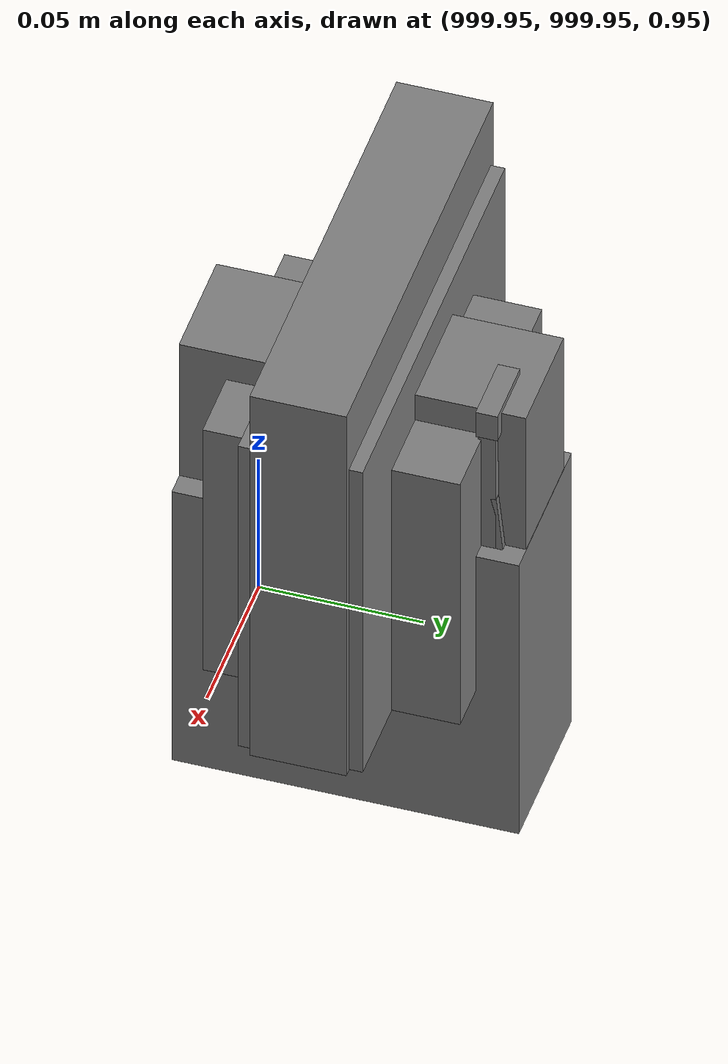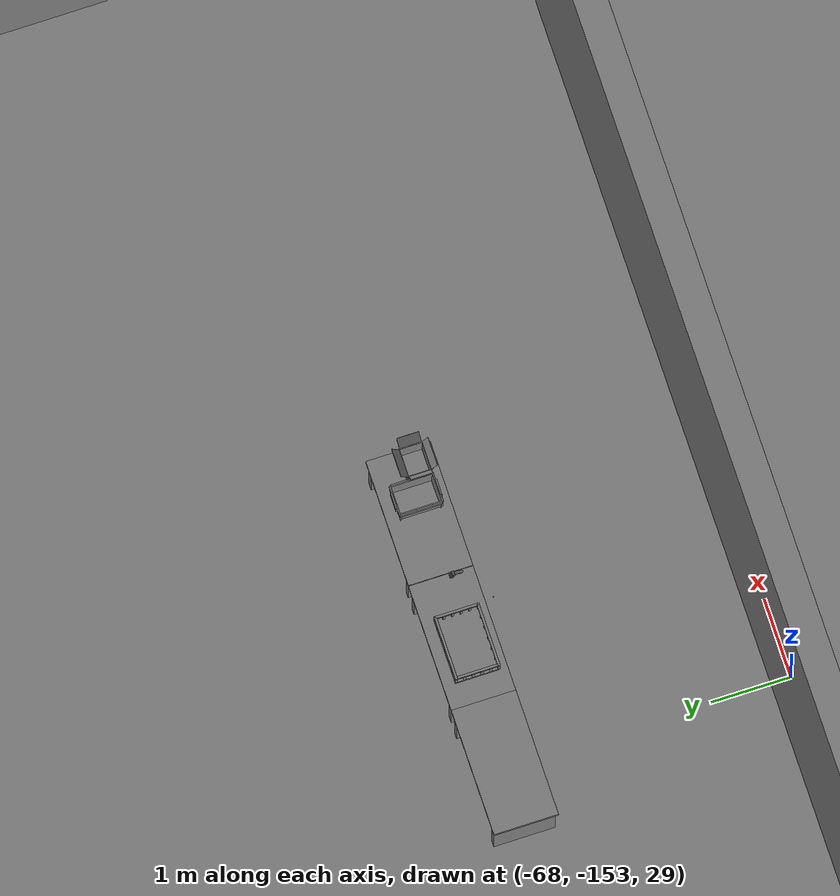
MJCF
<mujoco>
    <option gravity="0.000000000 0.000000000 -9.810000420" timestep="0.0049999999" integrator="implicitfast" density="1.225" viscosity="1.8000001e-05" noslip_iterations="10" iterations="100" sdf_iterations="50">
        <flag multiccd="disable"/>
    </option>
    <size memory="1000M"/>
    <compiler coordinate="local"/>
    <worldbody>
        <light cutoff="30" pos="0 1 1" dir="0 -1 -2"/>
        <light cutoff="30" pos="0 -1 1" dir="0 1 -2"/>
        <body pos="1000.000000000 1000.000000000 1.000000000" euler="0.000000000 0.000000000 180.000000000" name="openloong_gripper_2f85_fix_base_usda_battery_01">
            <geom contype="1" conaffinity="1" density="1000" type="box" material="" rgba="0.500000000 0.500000000 0.500000000 1.000000000" solimp="0.899999976 0.949999988 0.001000000" friction="1.000000000 0.005000000 0.000100000" solref="0.020000000 1.000000000" margin="0" condim="3" group="0" pos="-0.011123657 -0.041940309 0.101691343" quat="1.000000000 0.000000000 0.000000000 0.000000000" size="0.010800000 0.003375000 0.004725000" name="openloong_gripper_2f85_fix_base_usda_geom_E1D087AE_6876_422A_8E4F_03AA1A54E749"/>
            <geom contype="1" conaffinity="1" density="1000" type="box" material="" rgba="0.500000000 0.500000000 0.500000000 1.000000000" solimp="0.899999976 0.949999988 0.001000000" friction="1.000000000 0.005000000 0.000100000" solref="0.020000000 1.000000000" margin="0" condim="3" group="0" pos="-0.010876465 -0.044247437 0.047066893" quat="0.998702705 -0.050920475 0.000000000 0.000000000" size="0.009450001 0.002700000 0.024975000" name="openloong_gripper_2f85_fix_base_usda_geom_52B50297_430C_4630_884C_63881353777A"/>
            <geom contype="1" conaffinity="1" density="1000" type="box" material="" rgba="0.500000000 0.500000000 0.500000000 1.000000000" solimp="0.899999976 0.949999988 0.001000000" friction="1.000000000 0.005000000 0.000100000" solref="0.020000000 1.000000000" margin="0" condim="3" group="0" pos="-0.001235962 -0.000659180 0.047381196" quat="1.000000000 0.000000000 0.000000000 0.000000000" size="0.039420001 0.039150000 0.047250003" name="openloong_gripper_2f85_fix_base_usda_geom_9B3594D1_C3F9_4F66_85A2_6587B555C770"/>
            <geom contype="1" conaffinity="1" density="1000" type="box" material="" rgba="0.500000000 0.500000000 0.500000000 1.000000000" solimp="0.899999976 0.949999988 0.001000000" friction="1.000000000 0.005000000 0.000100000" solref="0.020000000 1.000000000" margin="0" condim="3" group="0" pos="-0.010876465 -0.039138794 0.009851727" quat="1.000000000 0.000000000 0.000000000 0.000000000" size="0.009450001 0.010800000 0.013500000" name="openloong_gripper_2f85_fix_base_usda_geom_8DB9FCF8_A62E_450C_9388_5078334FC6CF"/>
            <geom contype="1" conaffinity="1" density="1000" type="box" material="" rgba="0.500000000 0.500000000 0.500000000 1.000000000" solimp="0.899999976 0.949999988 0.001000000" friction="1.000000000 0.005000000 0.000100000" solref="0.020000000 1.000000000" margin="0" condim="3" group="0" pos="-0.010876465 -0.041528322 0.071508206" quat="1.000000000 0.000000000 0.000000000 0.000000000" size="0.009450001 0.002700000 0.027000001" name="openloong_gripper_2f85_fix_base_usda_geom_7BD8FAF9_C897_42F9_BE5D_1A039F89EEB7"/>
            <freejoint name="openloong_gripper_2f85_fix_base_usda_battery_01_joint"/>
            <site size="0.005000000 0.005000000 0.005000000" rgba="0.500000000 0.500000000 0.500000000 1.000000000" pos="0.000000000 0.000000000 0.000000000" quat="0.999961913 0.008726500 0.000000000 0.000000000" group="0" type="sphere" name="openloong_gripper_2f85_fix_base_usda_battery_01site"/>
        </body>
        <body pos="-66.232475281 -149.634658813 31.167381287" euler="176.713607788 -34.638519287 109.363357544" mocap="true" name="spotlight1_SpotLight"/>
        <body pos="1000.000000000 1000.000000000 1.000000000" euler="0.000000000 0.000000000 180.000000000" name="openloong_gripper_2f85_fix_base_usda_cpu_fan">
            <geom contype="1" conaffinity="1" density="1000" type="box" material="" rgba="0.500000000 0.500000000 0.500000000 1.000000000" solimp="0.899999976 0.949999988 0.001000000" friction="1.000000000 0.005000000 0.000100000" solref="0.020000000 1.000000000" margin="0" condim="3" group="0" pos="0.000000000 0.000000000 0.070034981" quat="0.000000000 0.000000000 0.000000000 1.000000000" size="0.070700005 0.014699999 0.070700005" name="openloong_gripper_2f85_fix_base_usda_geom_7DBD5720_1993_49BA_A493_839CDFED5F18"/>
            <freejoint name="openloong_gripper_2f85_fix_base_usda_cpu_fan_joint"/>
            <site size="0.005000000 0.005000000 0.005000000" rgba="0.500000000 0.500000000 0.500000000 1.000000000" pos="0.000000000 0.000000000 0.000000000" quat="0.999961913 0.008726535 0.000000000 0.000000000" group="0" type="sphere" name="openloong_gripper_2f85_fix_base_usda_cpu_fancsite"/>
        </body>
        <body pos="-66.262672424 -149.193740845 31.165187836" euler="-154.777145386 76.748420715 70.320915222" mocap="true" name="spotlight3_SpotLight"/>
        <body pos="1000.000000000 1000.000000000 1.000000000" euler="0.000000000 0.000000000 180.000000000" name="openloong_gripper_2f85_fix_base_usda_wifi_box">
            <geom contype="1" conaffinity="1" density="1000" type="box" material="" rgba="0.500000000 0.500000000 0.500000000 1.000000000" solimp="0.899999976 0.949999988 0.001000000" friction="1.000000000 0.005000000 0.000100000" solref="0.020000000 1.000000000" margin="0" condim="3" group="0" pos="0.000000000 0.000000000 0.058978677" quat="0.000000000 0.000000047 0.000000000 1.000000000" size="0.068499997 0.018999999 0.059000000" name="openloong_gripper_2f85_fix_base_usda_geom_EC2E6E5C_978F_4848_B33D_884C790CA1C2"/>
            <freejoint name="openloong_gripper_2f85_fix_base_usda_wifi_box_joint"/>
            <site size="0.005000000 0.005000000 0.005000000" rgba="0.500000000 0.500000000 0.500000000 1.000000000" pos="0.000000000 0.000000000 0.000000000" quat="0.999961913 0.008726500 0.000000000 0.000000000" group="0" type="sphere" name="openloong_gripper_2f85_fix_base_usda_wifi_boxsite"/>
        </body>
        <body pos="1000.000000000 1000.000000000 1.000000000" euler="0.000011953 0.000005123 -179.999984741" name="openloong_gripper_2f85_fix_base_usda_intel_box">
            <geom contype="1" conaffinity="1" density="1000" type="box" material="" rgba="0.500000000 0.500000000 0.500000000 1.000000000" solimp="0.899999976 0.949999988 0.001000000" friction="1.000000000 0.005000000 0.000100000" solref="0.020000000 1.000000000" margin="0" condim="3" group="0" pos="0.000000000 -0.000067139 0.000082284" quat="0.707106709 0.000000225 0.000000253 0.707106650" size="0.052800003 0.025300000 0.052800003" name="openloong_gripper_2f85_fix_base_usda_geom_2B6A9610_3894_4B0C_BBDD_41A5BF59F41E"/>
            <freejoint name="openloong_gripper_2f85_fix_base_usda_intel_box_joint"/>
            <site size="0.005000000 0.005000000 0.005000000" rgba="0.500000000 0.500000000 0.500000000 1.000000000" pos="0.000000000 0.000000000 0.000000000" quat="0.999961913 0.008726500 0.000000000 0.000000000" group="0" type="sphere" name="openloong_gripper_2f85_fix_base_usda_intel_boxsite"/>
        </body>
        <body pos="1000.000000000 999.999938965 1.000000000" euler="0.000000000 0.000000000 180.000000000" name="openloong_gripper_2f85_fix_base_usda_intelcore_i5">
            <geom contype="1" conaffinity="1" density="1000" type="box" material="" rgba="0.500000000 0.500000000 0.500000000 1.000000000" solimp="0.899999976 0.949999988 0.001000000" friction="1.000000000 0.005000000 0.000100000" solref="0.020000000 1.000000000" margin="0" condim="3" group="0" pos="0.000000000 0.000000000 0.051722717" quat="0.707106709 0.000000000 0.000000000 -0.707106769" size="0.052800000 0.018080002 0.052800000" name="openloong_gripper_2f85_fix_base_usda_geom_8BF43C94_F3BF_48D6_91E2_78BC89FF1A54"/>
            <freejoint name="openloong_gripper_2f85_fix_base_usda_intelcore_i5_joint"/>
            <site size="0.005000000 0.005000000 0.005000000" rgba="0.500000000 0.500000000 0.500000000 1.000000000" pos="0.000000000 0.000000000 0.000000000" quat="0.999961913 0.008726534 0.000000000 0.000000000" group="0" type="sphere" name="openloong_gripper_2f85_fix_base_usda_intelcore_i5site"/>
        </body>
        <body pos="-65.827148438 -148.972518921 31.166412354" euler="156.957015991 77.027870178 170.970886230" mocap="true" name="spotlight2_SpotLight"/>
        <body pos="-64.866622925 -149.383972168 30.183746338" euler="89.999984741 89.999946594 0.000000000" name="openloong_gripper_2f85_fix_base_usda_bluebox_01">
            <geom contype="1" conaffinity="1" density="1000" type="box" material="" rgba="0.500000000 0.500000000 0.500000000 1.000000000" solimp="0.899999976 0.949999988 0.001000000" friction="1.000000000 0.005000000 0.000100000" solref="0.020000000 1.000000000" margin="0" condim="3" group="0" pos="0.276580811 0.187225342 0.000068665" quat="0.707106948 0.000077471 0.707106352 0.000077486" size="0.100000001 0.057999998 0.010000000" name="openloong_gripper_2f85_fix_base_usda_geom_6E76EFFD_5135_438B_B329_905609F9535C"/>
            <geom contype="1" conaffinity="1" density="1000" type="box" material="" rgba="0.500000000 0.500000000 0.500000000 1.000000000" solimp="0.899999976 0.949999988 0.001000000" friction="1.000000000 0.005000000 0.000100000" solref="0.020000000 1.000000000" margin="0" condim="3" group="0" pos="0.000000000 0.002883911 0.000000000" quat="0.999999881 0.000000000 0.000000000 0.000000000" size="0.254000008 0.003000000 0.172000006" name="openloong_gripper_2f85_fix_base_usda_geom_6C9935A5_27AA_4445_93D4_3E456205A6B4"/>
            <geom contype="1" conaffinity="1" density="1000" type="box" material="" rgba="0.500000000 0.500000000 0.500000000 1.000000000" solimp="0.899999976 0.949999988 0.001000000" friction="1.000000000 0.005000000 0.000100000" solref="0.020000000 1.000000000" margin="0" condim="3" group="0" pos="0.000000000 0.124874115 0.173484802" quat="0.999796331 0.020176515 -0.000000015 0.000000030" size="0.259999990 0.119999997 0.007000000" name="openloong_gripper_2f85_fix_base_usda_geom_77043009_7723_4C1B_B785_71D47FAE4D9D"/>
            <geom contype="1" conaffinity="1" density="1000" type="box" material="" rgba="0.500000000 0.500000000 0.500000000 1.000000000" solimp="0.899999976 0.949999988 0.001000000" friction="1.000000000 0.005000000 0.000100000" solref="0.020000000 1.000000000" margin="0" condim="3" group="0" pos="0.000000000 0.124874115 -0.173469543" quat="0.999796331 -0.020176545 -0.000000015 0.000000000" size="0.259999990 0.119999997 0.007000000" name="openloong_gripper_2f85_fix_base_usda_geom_CEC6B2E9_794F_49F2_B2F4_DF6A29C4021E"/>
            <geom contype="1" conaffinity="1" density="1000" type="box" material="" rgba="0.500000000 0.500000000 0.500000000 1.000000000" solimp="0.899999976 0.949999988 0.001000000" friction="1.000000000 0.005000000 0.000100000" solref="0.020000000 1.000000000" margin="0" condim="3" group="0" pos="0.000000000 0.214008331 0.188980103" quat="0.999912977 0.013176724 0.000000015 0.000000000" size="0.259999990 0.029999999 0.012500000" name="openloong_gripper_2f85_fix_base_usda_geom_40C9CCBA_6B62_4B9A_8A52_D57D47AA674D"/>
            <geom contype="1" conaffinity="1" density="1000" type="box" material="" rgba="0.500000000 0.500000000 0.500000000 1.000000000" solimp="0.899999976 0.949999988 0.001000000" friction="1.000000000 0.005000000 0.000100000" solref="0.020000000 1.000000000" margin="0" condim="3" group="0" pos="-0.258361816 0.125289917 0.001876831" quat="0.702796936 -0.020792112 0.710783124 0.020769298" size="0.189999998 0.119999997 0.009000000" name="openloong_gripper_2f85_fix_base_usda_geom_86D96514_1553_42FF_85E0_0983CCE2990B"/>
            <geom contype="1" conaffinity="1" density="1000" type="box" material="" rgba="0.500000000 0.500000000 0.500000000 1.000000000" solimp="0.899999976 0.949999988 0.001000000" friction="1.000000000 0.005000000 0.000100000" solref="0.020000000 1.000000000" margin="0" condim="3" group="0" pos="0.000000000 0.214008331 -0.188980103" quat="0.999912977 -0.013176769 0.000000030 0.000000015" size="0.259999990 0.029999999 0.012500000" name="openloong_gripper_2f85_fix_base_usda_geom_4172B9EE_3CB0_444D_8E06_0FF02D46043C"/>
            <geom contype="1" conaffinity="1" density="1000" type="box" material="" rgba="0.500000000 0.500000000 0.500000000 1.000000000" solimp="0.899999976 0.949999988 0.001000000" friction="1.000000000 0.005000000 0.000100000" solref="0.020000000 1.000000000" margin="0" condim="3" group="0" pos="-0.276611328 0.187225342 0.000068665" quat="0.707106650 0.000077441 0.707106709 0.000077456" size="0.100000001 0.057999998 0.010000000" name="openloong_gripper_2f85_fix_base_usda_geom_72321849_7E73_43CF_9881_8E1C2C0435FE"/>
            <geom contype="1" conaffinity="1" density="1000" type="box" material="" rgba="0.500000000 0.500000000 0.500000000 1.000000000" solimp="0.899999976 0.949999988 0.001000000" friction="1.000000000 0.005000000 0.000100000" solref="0.020000000 1.000000000" margin="0" condim="3" group="0" pos="0.258331299 0.125289917 0.001876831" quat="0.702851415 0.018856421 0.710823774 -0.019329369" size="0.189999998 0.119999997 0.009000000" name="openloong_gripper_2f85_fix_base_usda_geom_9A2DBBE9_C743_4AC9_9640_936422372292"/>
            <freejoint name="openloong_gripper_2f85_fix_base_usda_bluebox_01_joint"/>
            <site size="0.005000000 0.005000000 0.005000000" rgba="0.500000000 0.500000000 0.500000000 1.000000000" pos="0.000000000 0.000000000 0.000000000" quat="0.999961913 0.008726534 0.000000000 0.000000000" group="0" type="sphere" name="openloong_gripper_2f85_fix_base_usda_bluebox_01site"/>
        </body>
        <body pos="-64.496299744 -149.491867065 30.235729218" euler="0.000000000 0.000000000 89.999946594" name="openloong_gripper_2f85_fix_base_usda_cardboardbox_01">
            <geom contype="1" conaffinity="1" density="1000" type="box" material="" rgba="0.500000000 0.500000000 0.500000000 1.000000000" solimp="0.899999976 0.949999988 0.001000000" friction="1.000000000 0.005000000 0.000100000" solref="0.020000000 1.000000000" margin="0" condim="3" group="0" pos="-0.003166199 -0.004086494 0.005052090" quat="1.000000000 0.000000000 0.000000000 0.000000000" size="0.142499998 0.177500010 0.005000000" name="openloong_gripper_2f85_fix_base_usda_geom_14AB0995_F8D8_4F07_968F_B48EFCF67768"/>
            <geom contype="1" conaffinity="1" density="1000" type="box" material="" rgba="0.500000000 0.500000000 0.500000000 1.000000000" solimp="0.899999976 0.949999988 0.001000000" friction="1.000000000 0.005000000 0.000100000" solref="0.020000000 1.000000000" margin="0" condim="3" group="0" pos="-0.003166199 0.170316696 0.150570869" quat="1.000000000 0.000000000 0.000000000 0.000000000" size="0.142499998 0.005000000 0.149999991" name="openloong_gripper_2f85_fix_base_usda_geom_4BACA980_1573_4A41_94C2_276B7E81ADFD"/>
            <geom contype="1" conaffinity="1" density="1000" type="box" material="" rgba="0.500000000 0.500000000 0.500000000 1.000000000" solimp="0.899999976 0.949999988 0.001000000" friction="1.000000000 0.005000000 0.000100000" solref="0.020000000 1.000000000" margin="0" condim="3" group="0" pos="-0.147399902 -0.005307198 0.150570869" quat="1.000000000 0.000000000 0.000000000 0.000000000" size="0.005000000 0.177500010 0.149999991" name="openloong_gripper_2f85_fix_base_usda_geom_CBE3D0E5_9731_40D0_82CD_EAEA92427E56"/>
            <geom contype="1" conaffinity="1" density="1000" type="box" material="" rgba="0.500000000 0.500000000 0.500000000 1.000000000" solimp="0.899999976 0.949999988 0.001000000" friction="1.000000000 0.005000000 0.000100000" solref="0.020000000 1.000000000" margin="0" condim="3" group="0" pos="0.140275955 -0.005307198 0.150570869" quat="1.000000000 0.000000000 0.000000000 0.000000000" size="0.005000000 0.177500010 0.149999991" name="openloong_gripper_2f85_fix_base_usda_geom_C493DB43_2D4E_43DA_BB5A_17BCA9757F07"/>
            <geom contype="1" conaffinity="1" density="1000" type="box" material="" rgba="0.500000000 0.500000000 0.500000000 1.000000000" solimp="0.899999976 0.949999988 0.001000000" friction="1.000000000 0.005000000 0.000100000" solref="0.020000000 1.000000000" margin="0" condim="3" group="0" pos="-0.003166199 -0.181550980 0.150570869" quat="1.000000000 0.000000000 0.000000000 0.000000000" size="0.142499998 0.005000000 0.149999991" name="openloong_gripper_2f85_fix_base_usda_geom_5A3383F9_37BE_47C3_AC6E_D2E914A2E922"/>
            <freejoint name="openloong_gripper_2f85_fix_base_usda_cardboardbox_01_joint"/>
            <site size="0.005000000 0.005000000 0.005000000" rgba="0.500000000 0.500000000 0.500000000 1.000000000" pos="0.000000000 0.000000000 0.000000000" quat="0.999961913 0.008726535 0.000000000 0.000000000" group="0" type="sphere" name="openloong_gripper_2f85_fix_base_usda_site_F053B0A2_D95B_4B62_BD09_572FD8E8FDEE"/>
            <body pos="0.139160156 -0.004048347 0.301930904" euler="-179.999954224 49.383502960 179.999954224" name="openloong_gripper_2f85_fix_base_usda_A1_006">
                <geom contype="1" conaffinity="1" density="1000" type="box" material="" rgba="0.500000000 0.500000000 0.500000000 1.000000000" solimp="0.899999976 0.949999988 0.001000000" friction="1.000000000 0.005000000 0.000100000" solref="0.020000000 1.000000000" margin="0" condim="3" group="0" pos="-0.071587563 0.000009537 0.001745224" quat="0.999999881 0.000000000 0.000000000 0.000000000" size="0.071249999 0.179999992 0.002500000" name="openloong_gripper_2f85_fix_base_usda_geom_09D8A2CB_DB60_413F_B261_43B52C742BF6"/>
                <joint armature="0" stiffness="0.07" damping="0.0099999998" axis="0.000000 1.000000 0.000000" type="hinge" name="openloong_gripper_2f85_fix_base_usda_A1_006"/>
            </body>
            <body pos="-0.145902634 -0.004086494 0.301938057" euler="-180.000000000 -60.000011444 -180.000000000" name="openloong_gripper_2f85_fix_base_usda_A2_006">
                <geom contype="1" conaffinity="1" density="1000" type="box" material="" rgba="0.500000000 0.500000000 0.500000000 1.000000000" solimp="0.899999976 0.949999988 0.001000000" friction="1.000000000 0.005000000 0.000100000" solref="0.020000000 1.000000000" margin="0" condim="3" group="0" pos="0.071268082 0.000009537 0.002717972" quat="0.000002921 0.000000000 -0.000000030 0.999999881" size="0.071249999 0.179999992 0.002500000" name="openloong_gripper_2f85_fix_base_usda_geom_B862D027_B562_49B4_A0AE_370F9CED6A87"/>
                <joint armature="0" stiffness="0.07" damping="0.0099999998" axis="0.000000 1.000000 0.000000" type="hinge" name="openloong_gripper_2f85_fix_base_usda_A2_006"/>
            </body>
            <body pos="-0.003385544 0.175991058 0.301930904" euler="-125.858116150 -0.000004561 0.000002331" name="openloong_gripper_2f85_fix_base_usda_B2_006">
                <geom contype="1" conaffinity="1" density="1000" type="box" material="" rgba="0.500000000 0.500000000 0.500000000 1.000000000" solimp="0.899999976 0.949999988 0.001000000" friction="1.000000000 0.005000000 0.000100000" solref="0.020000000 1.000000000" margin="0" condim="3" group="0" pos="0.000009537 -0.070939064 -0.002470016" quat="0.999614120 0.027776197 -0.000000015 0.000000030" size="0.137500003 0.064999998 0.005000000" name="openloong_gripper_2f85_fix_base_usda_geom_F5023B6B_31D5_4E51_9DB6_D3B4630DDD12"/>
                <joint armature="0" stiffness="0.07" damping="0.0099999998" axis="1.000000 0.000000 0.000000" type="hinge" name="openloong_gripper_2f85_fix_base_usda_B2_006"/>
            </body>
            <body pos="-0.003385544 -0.184140205 0.301938057" euler="147.805557251 0.000000000 0.000000000" name="openloong_gripper_2f85_fix_base_usda_B1_006">
                <geom contype="1" conaffinity="1" density="1000" type="box" material="" rgba="0.500000000 0.500000000 0.500000000 1.000000000" solimp="0.899999976 0.949999988 0.001000000" friction="1.000000000 0.005000000 0.000100000" solref="0.020000000 1.000000000" margin="0" condim="3" group="0" pos="-0.000028610 0.070202351 -0.002703667" quat="0.999614179 -0.027776167 0.000000000 0.000000000" size="0.137500003 0.064999998 0.005000000" name="openloong_gripper_2f85_fix_base_usda_geom_8A7D6591_74B5_4A69_B8BE_033D8ADA386A"/>
                <joint armature="0" stiffness="0.07" damping="0.0099999998" axis="1.000000 0.000000 0.000000" type="hinge" name="openloong_gripper_2f85_fix_base_usda_B1_006"/>
            </body>
        </body>
        <body pos="-65.882858276 -149.481979370 30.229999542" euler="-64.487716675 0.000000000 0.000000000" name="openloong_gripper_2f85_fix_base_usda_Barcode">
            <geom contype="1" conaffinity="1" density="1000" type="box" material="" rgba="0.500000000 0.500000000 0.500000000 1.000000000" solimp="0.899999976 0.949999988 0.001000000" friction="1.000000000 0.005000000 0.000100000" solref="0.020000000 1.000000000" margin="0" condim="3" group="0" pos="0.000000000 0.013038635 0.001419067" quat="0.000000000 0.000000000 0.000000000 1.000000119" size="0.034000002 0.010000000 0.017999999" name="openloong_gripper_2f85_fix_base_usda_geom_9870896F_3F2F_44ED_B7E8_8DD24499C7A9"/>
            <geom contype="1" conaffinity="1" density="1000" type="box" material="" rgba="0.500000000 0.500000000 0.500000000 1.000000000" solimp="0.899999976 0.949999988 0.001000000" friction="1.000000000 0.005000000 0.000100000" solref="0.020000000 1.000000000" margin="0" condim="3" group="0" pos="0.000000000 -0.035301208 -0.007095337" quat="0.000000000 0.000000000 -0.043619365 0.999048233" size="0.028999999 0.010000000 0.020000000" name="openloong_gripper_2f85_fix_base_usda_geom_38C25490_3C41_4909_995C_EFE21DA2B387"/>
            <geom contype="1" conaffinity="1" density="1000" type="box" material="" rgba="0.500000000 0.500000000 0.500000000 1.000000000" solimp="0.899999976 0.949999988 0.001000000" friction="1.000000000 0.005000000 0.000100000" solref="0.020000000 1.000000000" margin="0" condim="3" group="0" pos="0.000000000 -0.043411255 -0.011749268" quat="0.922262907 0.386563420 0.000000000 0.000000000" size="0.026000001 0.010000000 0.020000000" name="openloong_gripper_2f85_fix_base_usda_geom_4C3C40C4_78CB_49F8_AF8B_8656D9CC0B23"/>
            <geom contype="1" conaffinity="1" density="1000" type="box" material="" rgba="0.500000000 0.500000000 0.500000000 1.000000000" solimp="0.899999976 0.949999988 0.001000000" friction="1.000000000 0.005000000 0.000100000" solref="0.020000000 1.000000000" margin="0" condim="3" group="0" pos="0.000000000 -0.016967773 -0.031860352" quat="0.000000000 0.000000000 0.000000000 1.000000119" size="0.008000000 0.010000000 0.013000000" name="openloong_gripper_2f85_fix_base_usda_geom_47488BC2_A832_43B4_9457_AFAC19752672"/>
            <geom contype="1" conaffinity="1" density="1000" type="box" material="" rgba="0.500000000 0.500000000 0.500000000 1.000000000" solimp="0.899999976 0.949999988 0.001000000" friction="1.000000000 0.005000000 0.000100000" solref="0.020000000 1.000000000" margin="0" condim="3" group="0" pos="0.000000000 -0.001869202 0.000312805" quat="0.953716993 0.300705761 0.000000000 0.000000000" size="0.032000002 0.010000000 0.018999999" name="openloong_gripper_2f85_fix_base_usda_geom_4FF8AC37_C886_4076_8E60_BEF0D10DE218"/>
            <geom contype="1" conaffinity="1" density="1000" type="box" material="" rgba="0.500000000 0.500000000 0.500000000 1.000000000" solimp="0.899999976 0.949999988 0.001000000" friction="1.000000000 0.005000000 0.000100000" solref="0.020000000 1.000000000" margin="0" condim="3" group="0" pos="0.000000000 -0.019531250 -0.003173828" quat="0.953716993 0.300705761 0.000000000 0.000000000" size="0.030999999 0.010000000 0.020000000" name="openloong_gripper_2f85_fix_base_usda_geom_E79B6A8B_C6AC_4932_8EBA_BD3465509CD9"/>
            <geom contype="1" conaffinity="1" density="1000" type="box" material="" rgba="0.500000000 0.500000000 0.500000000 1.000000000" solimp="0.899999976 0.949999988 0.001000000" friction="1.000000000 0.005000000 0.000100000" solref="0.020000000 1.000000000" margin="0" condim="3" group="0" pos="0.000000000 -0.035301208 -0.007095337" quat="0.953716993 0.300705761 0.000000000 0.000000000" size="0.028999999 0.010000000 0.020000000" name="openloong_gripper_2f85_fix_base_usda_geom_1E3DD024_A697_4AB1_BAA7_7CD52A16F5B4"/>
            <geom contype="1" conaffinity="1" density="1000" type="box" material="" rgba="0.500000000 0.500000000 0.500000000 1.000000000" solimp="0.899999976 0.949999988 0.001000000" friction="1.000000000 0.005000000 0.000100000" solref="0.020000000 1.000000000" margin="0" condim="3" group="0" pos="0.000000000 -0.042617798 -0.071121216" quat="0.000000000 0.000000000 0.000000000 1.000000119" size="0.013000000 0.021000000 0.059999999" name="openloong_gripper_2f85_fix_base_usda_geom_F973358B_970E_4C5E_953D_7BFCDFD0C185"/>
            <freejoint name="openloong_gripper_2f85_fix_base_usda_Barcode_joint"/>
            <site size="0.005000000 0.005000000 0.005000000" rgba="0.500000000 0.500000000 0.500000000 1.000000000" pos="0.000000000 0.000000000 0.000000000" quat="1.000000000 0.000000000 0.000000000 0.000000000" group="0" type="sphere" name="openloong_gripper_2f85_fix_base_usda_Barcode_site"/>
        </body>
        <body pos="-66.745018005 -149.392349243 30.184000015" euler="0.000000000 0.000000000 89.999946594" name="[22332885972529]_Basket_01">
            <geom contype="1" conaffinity="1" density="1000" type="box" material="" rgba="0.500000000 0.500000000 0.500000000 1.000000000" solimp="0.899999976 0.949999988 0.001000000" friction="1.000000000 0.005000000 0.000100000" solref="0.020000000 1.000000000" margin="0" condim="3" group="0" pos="-0.052425385 0.389207840 0.089787483" quat="0.707107008 0.000000000 0.000000000 0.707106411" size="0.014249999 0.014249999 0.059999999" name="[22332885972529]_geom_CACDFC0E_4832_48F2_BF65_F28FC7164ACA"/>
            <geom contype="1" conaffinity="1" density="1000" type="box" material="" rgba="0.500000000 0.500000000 0.500000000 1.000000000" solimp="0.899999976 0.949999988 0.001000000" friction="1.000000000 0.005000000 0.000100000" solref="0.020000000 1.000000000" margin="0" condim="3" group="0" pos="0.264015198 -0.133043289 0.089787483" quat="0.707107008 0.000000000 0.000000000 0.707106411" size="0.014249999 0.014249999 0.059999999" name="[22332885972529]_geom_B11F987F_EBD9_49BD_ABAB_D42B33D8887A"/>
            <geom contype="1" conaffinity="1" density="1000" type="box" material="" rgba="0.500000000 0.500000000 0.500000000 1.000000000" solimp="0.899999976 0.949999988 0.001000000" friction="1.000000000 0.005000000 0.000100000" solref="0.020000000 1.000000000" margin="0" condim="3" group="0" pos="-0.264015198 -0.265548706 0.089793205" quat="0.707107008 0.000000000 0.000000000 0.707106411" size="0.014249999 0.014249999 0.059999999" name="[22332885972529]_geom_1774B636_796D_430D_BFAB_4CBB01AFD90E"/>
            <geom contype="1" conaffinity="1" density="1000" type="box" material="" rgba="0.500000000 0.500000000 0.500000000 1.000000000" solimp="0.899999976 0.949999988 0.001000000" friction="1.000000000 0.005000000 0.000100000" solref="0.020000000 1.000000000" margin="0" condim="3" group="0" pos="-0.160263062 -0.389322281 0.089793205" quat="0.707107008 0.000000000 0.000000000 0.707106411" size="0.014249999 0.014249999 0.059999999" name="[22332885972529]_geom_FD31E9D9_26B5_4CE3_8F07_CF15D31CFEC4"/>
            <geom contype="1" conaffinity="1" density="1000" type="box" material="" rgba="0.500000000 0.500000000 0.500000000 1.000000000" solimp="0.899999976 0.949999988 0.001000000" friction="1.000000000 0.005000000 0.000100000" solref="0.020000000 1.000000000" margin="0" condim="3" group="0" pos="0.162265778 -0.389322281 0.089787483" quat="0.707107008 0.000000000 0.000000000 0.707106411" size="0.014249999 0.014249999 0.059999999" name="[22332885972529]_geom_AEBD9FD9_4739_45D8_A715_663F777C672C"/>
            <geom contype="1" conaffinity="1" density="1000" type="box" material="" rgba="0.500000000 0.500000000 0.500000000 1.000000000" solimp="0.899999976 0.949999988 0.001000000" friction="1.000000000 0.005000000 0.000100000" solref="0.020000000 1.000000000" margin="0" condim="3" group="0" pos="0.264015198 0.389207840 0.089787483" quat="0.707107008 0.000000000 0.000000000 0.707106411" size="0.014249999 0.014249999 0.059999999" name="[22332885972529]_geom_24846BC9_8820_4775_B183_7E0D6EF262D2"/>
            <geom contype="1" conaffinity="1" density="1000" type="box" material="" rgba="0.500000000 0.500000000 0.500000000 1.000000000" solimp="0.899999976 0.949999988 0.001000000" friction="1.000000000 0.005000000 0.000100000" solref="0.020000000 1.000000000" margin="0" condim="3" group="0" pos="-0.264015198 -0.133043289 0.089793205" quat="0.707107008 0.000000000 0.000000000 0.707106411" size="0.014249999 0.014249999 0.059999999" name="[22332885972529]_geom_4CC7F25E_07B8_4265_BC18_B96BDCE40813"/>
            <geom contype="1" conaffinity="1" density="1000" type="box" material="" rgba="0.500000000 0.500000000 0.500000000 1.000000000" solimp="0.899999976 0.949999988 0.001000000" friction="1.000000000 0.005000000 0.000100000" solref="0.020000000 1.000000000" margin="0" condim="3" group="0" pos="-0.264026642 0.269256592 0.089793205" quat="0.707107008 0.000000000 0.000000000 0.707106411" size="0.014249999 0.014249999 0.059999999" name="[22332885972529]_geom_CDF8EDAA_5F1C_4EB1_A068_20122793224D"/>
            <geom contype="1" conaffinity="1" density="1000" type="box" material="" rgba="0.500000000 0.500000000 0.500000000 1.000000000" solimp="0.899999976 0.949999988 0.001000000" friction="1.000000000 0.005000000 0.000100000" solref="0.020000000 1.000000000" margin="0" condim="3" group="0" pos="0.054462433 0.389207840 0.089787483" quat="0.707107008 0.000000000 0.000000000 0.707106411" size="0.014249999 0.014249999 0.059999999" name="[22332885972529]_geom_8178E378_A291_4F68_B303_BDA4BD259BA3"/>
            <geom contype="1" conaffinity="1" density="1000" type="box" material="" rgba="0.500000000 0.500000000 0.500000000 1.000000000" solimp="0.899999976 0.949999988 0.001000000" friction="1.000000000 0.005000000 0.000100000" solref="0.020000000 1.000000000" margin="0" condim="3" group="0" pos="0.054462433 -0.389322281 0.089787483" quat="0.707107008 0.000000000 0.000000000 0.707106411" size="0.014249999 0.014249999 0.059999999" name="[22332885972529]_geom_264A0DB7_2B74_47A3_A7F7_BFA9B00CCB65"/>
            <geom contype="1" conaffinity="1" density="1000" type="box" material="" rgba="0.500000000 0.500000000 0.500000000 1.000000000" solimp="0.899999976 0.949999988 0.001000000" friction="1.000000000 0.005000000 0.000100000" solref="0.020000000 1.000000000" margin="0" condim="3" group="0" pos="0.264015198 0.269256592 0.089793205" quat="0.707107008 0.000000000 0.000000000 0.707106411" size="0.014249999 0.014249999 0.059999999" name="[22332885972529]_geom_113D4B93_49D7_454A_A63F_5593550E57AE"/>
            <geom contype="1" conaffinity="1" density="1000" type="box" material="" rgba="0.500000000 0.500000000 0.500000000 1.000000000" solimp="0.899999976 0.949999988 0.001000000" friction="1.000000000 0.005000000 0.000100000" solref="0.020000000 1.000000000" margin="0" condim="3" group="0" pos="0.264015198 -0.389322281 0.089787483" quat="0.707107008 0.000000000 0.000000000 0.707106411" size="0.014249999 0.014249999 0.059999999" name="[22332885972529]_geom_C49561C7_CE8D_47ED_A341_6A760A5BBB9C"/>
            <geom contype="1" conaffinity="1" density="1000" type="box" material="" rgba="0.500000000 0.500000000 0.500000000 1.000000000" solimp="0.899999976 0.949999988 0.001000000" friction="1.000000000 0.005000000 0.000100000" solref="0.020000000 1.000000000" margin="0" condim="3" group="0" pos="0.000000000 0.000000000 0.015998840" quat="0.707107008 0.000000000 0.000000000 0.707106411" size="0.403499991 0.279000014 0.015750000" name="[22332885972529]_geom_F3FD5334_4A0A_4D2A_883F_410703530588"/>
            <geom contype="1" conaffinity="1" density="1000" type="box" material="" rgba="0.500000000 0.500000000 0.500000000 1.000000000" solimp="0.899999976 0.949999988 0.001000000" friction="1.000000000 0.005000000 0.000100000" solref="0.020000000 1.000000000" margin="0" condim="3" group="0" pos="0.000000000 -0.389476776 0.163619041" quat="0.707107008 0.000000000 0.000000000 0.707106411" size="0.015000000 0.277500004 0.015750000" name="[22332885972529]_geom_0AFD22FB_DD32_4B0A_9AE8_9783D99A3354"/>
            <geom contype="1" conaffinity="1" density="1000" type="box" material="" rgba="0.500000000 0.500000000 0.500000000 1.000000000" solimp="0.899999976 0.949999988 0.001000000" friction="1.000000000 0.005000000 0.000100000" solref="0.020000000 1.000000000" margin="0" condim="3" group="0" pos="0.162265778 0.389207840 0.089787483" quat="0.707107008 0.000000000 0.000000000 0.707106411" size="0.014249999 0.014249999 0.059999999" name="[22332885972529]_geom_BC51834B_6414_49FA_A7B1_D6517CEBBA25"/>
            <geom contype="1" conaffinity="1" density="1000" type="box" material="" rgba="0.500000000 0.500000000 0.500000000 1.000000000" solimp="0.899999976 0.949999988 0.001000000" friction="1.000000000 0.005000000 0.000100000" solref="0.020000000 1.000000000" margin="0" condim="3" group="0" pos="0.000000000 0.389471054 0.163619041" quat="0.707107008 0.000000000 0.000000000 0.707106411" size="0.015000000 0.277500004 0.015750000" name="[22332885972529]_geom_24FF497F_B152_4986_A275_6F3523A41620"/>
            <geom contype="1" conaffinity="1" density="1000" type="box" material="" rgba="0.500000000 0.500000000 0.500000000 1.000000000" solimp="0.899999976 0.949999988 0.001000000" friction="1.000000000 0.005000000 0.000100000" solref="0.020000000 1.000000000" margin="0" condim="3" group="0" pos="-0.263511658 0.000000000 0.163619041" quat="0.707107008 0.000000000 0.000000000 0.707106411" size="0.403499991 0.015000000 0.015750000" name="[22332885972529]_geom_CC7B5049_A99C_416C_A094_489FF28A2C4F"/>
            <geom contype="1" conaffinity="1" density="1000" type="box" material="" rgba="0.500000000 0.500000000 0.500000000 1.000000000" solimp="0.899999976 0.949999988 0.001000000" friction="1.000000000 0.005000000 0.000100000" solref="0.020000000 1.000000000" margin="0" condim="3" group="0" pos="-0.264015198 0.141334534 0.089793205" quat="0.707107008 0.000000000 0.000000000 0.707106411" size="0.014249999 0.014249999 0.059999999" name="[22332885972529]_geom_2F9C2C92_6F6F_405A_807F_B10F66B0721E"/>
            <geom contype="1" conaffinity="1" density="1000" type="box" material="" rgba="0.500000000 0.500000000 0.500000000 1.000000000" solimp="0.899999976 0.949999988 0.001000000" friction="1.000000000 0.005000000 0.000100000" solref="0.020000000 1.000000000" margin="0" condim="3" group="0" pos="0.264015198 -0.265548706 0.089787483" quat="0.707107008 0.000000000 0.000000000 0.707106411" size="0.014249999 0.014249999 0.059999999" name="[22332885972529]_geom_E9631124_19F2_445A_8EC6_97205B46FC3A"/>
            <geom contype="1" conaffinity="1" density="1000" type="box" material="" rgba="0.500000000 0.500000000 0.500000000 1.000000000" solimp="0.899999976 0.949999988 0.001000000" friction="1.000000000 0.005000000 0.000100000" solref="0.020000000 1.000000000" margin="0" condim="3" group="0" pos="-0.160263062 0.389207840 0.089787483" quat="0.707107008 0.000000000 0.000000000 0.707106411" size="0.014249999 0.014249999 0.059999999" name="[22332885972529]_geom_4726B353_C579_4D10_B204_01FD6C10AC82"/>
            <geom contype="1" conaffinity="1" density="1000" type="box" material="" rgba="0.500000000 0.500000000 0.500000000 1.000000000" solimp="0.899999976 0.949999988 0.001000000" friction="1.000000000 0.005000000 0.000100000" solref="0.020000000 1.000000000" margin="0" condim="3" group="0" pos="-0.052425385 -0.389322281 0.089787483" quat="0.707107008 0.000000000 0.000000000 0.707106411" size="0.014249999 0.014249999 0.059999999" name="[22332885972529]_geom_54779C88_C8DF_491E_97D6_56D81EEC4ADC"/>
            <geom contype="1" conaffinity="1" density="1000" type="box" material="" rgba="0.500000000 0.500000000 0.500000000 1.000000000" solimp="0.899999976 0.949999988 0.001000000" friction="1.000000000 0.005000000 0.000100000" solref="0.020000000 1.000000000" margin="0" condim="3" group="0" pos="-0.264026642 -0.389322281 0.089793205" quat="0.707107008 0.000000000 0.000000000 0.707106411" size="0.014249999 0.014249999 0.059999999" name="[22332885972529]_geom_77207EBB_24DB_41DA_98BD_D34E6B43B8EB"/>
            <geom contype="1" conaffinity="1" density="1000" type="box" material="" rgba="0.500000000 0.500000000 0.500000000 1.000000000" solimp="0.899999976 0.949999988 0.001000000" friction="1.000000000 0.005000000 0.000100000" solref="0.020000000 1.000000000" margin="0" condim="3" group="0" pos="0.264015198 0.141334534 0.089787483" quat="0.707107008 0.000000000 0.000000000 0.707106411" size="0.014249999 0.014249999 0.059999999" name="[22332885972529]_geom_61F96C35_D1B5_463F_900F_DE82B748E296"/>
            <geom contype="1" conaffinity="1" density="1000" type="box" material="" rgba="0.500000000 0.500000000 0.500000000 1.000000000" solimp="0.899999976 0.949999988 0.001000000" friction="1.000000000 0.005000000 0.000100000" solref="0.020000000 1.000000000" margin="0" condim="3" group="0" pos="-0.264015198 0.389207840 0.089793205" quat="0.707107008 0.000000000 0.000000000 0.707106411" size="0.014249999 0.014249999 0.059999999" name="[22332885972529]_geom_99623798_EB55_43AC_A213_B312EE6898B0"/>
            <geom contype="1" conaffinity="1" density="1000" type="box" material="" rgba="0.500000000 0.500000000 0.500000000 1.000000000" solimp="0.899999976 0.949999988 0.001000000" friction="1.000000000 0.005000000 0.000100000" solref="0.020000000 1.000000000" margin="0" condim="3" group="0" pos="0.264015198 0.004480362 0.089787483" quat="0.707107008 0.000000000 0.000000000 0.707106411" size="0.014249999 0.014249999 0.059999999" name="[22332885972529]_geom_735937E8_B947_43CC_A6FC_2CCEE85E273F"/>
            <geom contype="1" conaffinity="1" density="1000" type="box" material="" rgba="0.500000000 0.500000000 0.500000000 1.000000000" solimp="0.899999976 0.949999988 0.001000000" friction="1.000000000 0.005000000 0.000100000" solref="0.020000000 1.000000000" margin="0" condim="3" group="0" pos="0.263694763 -0.000011444 0.163619041" quat="0.707107008 0.000000000 0.000000000 0.707106411" size="0.403499991 0.015000000 0.015750000" name="[22332885972529]_geom_C19B4758_D70A_4C8D_8927_132A28B468F8"/>
            <geom contype="1" conaffinity="1" density="1000" type="box" material="" rgba="0.500000000 0.500000000 0.500000000 1.000000000" solimp="0.899999976 0.949999988 0.001000000" friction="1.000000000 0.005000000 0.000100000" solref="0.020000000 1.000000000" margin="0" condim="3" group="0" pos="-0.264015198 0.004480362 0.089793205" quat="0.707107008 0.000000000 0.000000000 0.707106411" size="0.014249999 0.014249999 0.059999999" name="[22332885972529]_geom_B5F693F9_0406_44AD_9369_67609EFA6052"/>
            <freejoint name="[22332885972529]_joint_62943538_A37A_4F27_8EEA_5A69783CC8D8"/>
        </body>
        <body pos="0.000000000 0.000000000 0.000000000" euler="0.000000000 0.000000000 0.000000000" name="Static Objects_Static Objects">
            <geom contype="1" conaffinity="1" density="1000" type="box" material="" rgba="0.500000000 0.500000000 0.500000000 1.000000000" solimp="0.899999976 0.949999988 0.001000000" friction="1.000000000 0.005000000 0.000100000" solref="0.020000000 1.000000000" margin="0" condim="3" group="0" pos="-67.544113159 -149.365814209 29.727830887" quat="0.500000417 0.499999970 0.499999553 0.499999970" size="0.381000012 0.319999993 0.041000001" name="Static Objects_geom_E8B10DA2_1DA6_431B_89A4_9ED4CA084595"/>
            <geom contype="1" conaffinity="1" density="1000" type="box" material="" rgba="0.500000000 0.500000000 0.500000000 1.000000000" solimp="0.899999976 0.949999988 0.001000000" friction="1.000000000 0.005000000 0.000100000" solref="0.020000000 1.000000000" margin="0" condim="3" group="0" pos="-68.239501953 -149.365814209 30.086868286" quat="0.500000417 0.499999970 0.499999553 0.499999970" size="0.370999992 0.039500002 0.745000005" name="Static Objects_geom_0C4DD30E_BAAE_4B74_8D4F_FEA1B254F510"/>
            <geom contype="1" conaffinity="1" density="1000" type="box" material="" rgba="0.500000000 0.500000000 0.500000000 1.000000000" solimp="0.899999976 0.949999988 0.001000000" friction="1.000000000 0.005000000 0.000100000" solref="0.020000000 1.000000000" margin="0" condim="3" group="0" pos="-68.239501953 -149.365814209 30.147235870" quat="0.500000417 0.499999970 0.499999553 0.499999970" size="0.400000006 0.022000000 0.800000012" name="Static Objects_geom_256E6221_94FD_4541_9B7C_1351C19579F6"/>
            <geom contype="1" conaffinity="1" density="1000" type="box" material="" rgba="0.500000000 0.500000000 0.500000000 1.000000000" solimp="0.899999976 0.949999988 0.001000000" friction="1.000000000 0.005000000 0.000100000" solref="0.020000000 1.000000000" margin="0" condim="3" group="0" pos="-68.934890747 -149.365814209 29.727830887" quat="0.500000417 0.499999970 0.499999553 0.499999970" size="0.381000012 0.319999993 0.041000001" name="Static Objects_geom_33CFE432_1574_41CA_9D0E_E96E30D571EB"/>
            <geom contype="1" conaffinity="1" density="1000" type="box" material="" rgba="0.500000000 0.500000000 0.500000000 1.000000000" solimp="0.899999976 0.949999988 0.001000000" friction="1.000000000 0.005000000 0.000100000" solref="0.020000000 1.000000000" margin="0" condim="3" group="0" pos="-68.239501953 -149.365814209 29.561563492" quat="0.500000417 0.499999970 0.499999553 0.499999970" size="0.020000000 0.022000000 0.660000026" name="Static Objects_geom_1DBE4A42_8029_4B9D_9482_0FEE77BCDC19"/>
            <geom contype="1" conaffinity="1" density="1000" type="box" material="" rgba="0.500000000 0.500000000 0.500000000 1.000000000" solimp="0.899999976 0.949999988 0.001000000" friction="1.000000000 0.005000000 0.000100000" solref="0.020000000 1.000000000" margin="0" condim="3" group="0" pos="-65.945671082 -149.365814209 29.727830887" quat="0.500000417 0.499999970 0.499999553 0.499999970" size="0.381000012 0.319999993 0.041000001" name="Static Objects_geom_E6526883_B7BA_42F2_B838_FE818E2CB7A3"/>
            <geom contype="1" conaffinity="1" density="1000" type="box" material="" rgba="0.500000000 0.500000000 0.500000000 1.000000000" solimp="0.899999976 0.949999988 0.001000000" friction="1.000000000 0.005000000 0.000100000" solref="0.020000000 1.000000000" margin="0" condim="3" group="0" pos="-66.641059875 -149.365814209 30.086868286" quat="0.500000417 0.499999970 0.499999553 0.499999970" size="0.370999992 0.039500002 0.745000005" name="Static Objects_geom_7006731F_C98E_4BC7_B309_7D165B4EB32E"/>
            <geom contype="1" conaffinity="1" density="1000" type="box" material="" rgba="0.500000000 0.500000000 0.500000000 1.000000000" solimp="0.899999976 0.949999988 0.001000000" friction="1.000000000 0.005000000 0.000100000" solref="0.020000000 1.000000000" margin="0" condim="3" group="0" pos="-66.641059875 -149.365814209 30.147235870" quat="0.500000417 0.499999970 0.499999553 0.499999970" size="0.400000006 0.022000000 0.800000012" name="Static Objects_geom_C4196D79_B359_497A_9F4E_292FD92B22B4"/>
            <geom contype="1" conaffinity="1" density="1000" type="box" material="" rgba="0.500000000 0.500000000 0.500000000 1.000000000" solimp="0.899999976 0.949999988 0.001000000" friction="1.000000000 0.005000000 0.000100000" solref="0.020000000 1.000000000" margin="0" condim="3" group="0" pos="-67.336448669 -149.365814209 29.727830887" quat="0.500000417 0.499999970 0.499999553 0.499999970" size="0.381000012 0.319999993 0.041000001" name="Static Objects_geom_938D6D09_D5BD_454F_9291_B49E9C31DE17"/>
            <geom contype="1" conaffinity="1" density="1000" type="box" material="" rgba="0.500000000 0.500000000 0.500000000 1.000000000" solimp="0.899999976 0.949999988 0.001000000" friction="1.000000000 0.005000000 0.000100000" solref="0.020000000 1.000000000" margin="0" condim="3" group="0" pos="-66.641059875 -149.365814209 29.561563492" quat="0.500000417 0.499999970 0.499999553 0.499999970" size="0.020000000 0.022000000 0.660000026" name="Static Objects_geom_E9680ACE_5E82_43B7_AF9A_7652405BDD2F"/>
            <geom contype="1" conaffinity="1" density="1000" type="box" material="" rgba="0.500000000 0.500000000 0.500000000 1.000000000" solimp="0.899999976 0.949999988 0.001000000" friction="1.000000000 0.005000000 0.000100000" solref="0.020000000 1.000000000" margin="0" condim="3" group="0" pos="-64.338577271 -149.365814209 29.727830887" quat="0.500000417 0.499999970 0.499999553 0.499999970" size="0.381000012 0.319999993 0.041000001" name="Static Objects_geom_34B80266_865D_40B1_92E4_576FBD4A53DC"/>
            <geom contype="1" conaffinity="1" density="1000" type="box" material="" rgba="0.500000000 0.500000000 0.500000000 1.000000000" solimp="0.899999976 0.949999988 0.001000000" friction="1.000000000 0.005000000 0.000100000" solref="0.020000000 1.000000000" margin="0" condim="3" group="0" pos="-65.033966064 -149.365814209 30.086868286" quat="0.500000417 0.499999970 0.499999553 0.499999970" size="0.370999992 0.039500002 0.745000005" name="Static Objects_geom_2E022BEB_8D31_49E2_A746_A089F04DADB4"/>
            <geom contype="1" conaffinity="1" density="1000" type="box" material="" rgba="0.500000000 0.500000000 0.500000000 1.000000000" solimp="0.899999976 0.949999988 0.001000000" friction="1.000000000 0.005000000 0.000100000" solref="0.020000000 1.000000000" margin="0" condim="3" group="0" pos="-65.033966064 -149.365814209 30.147235870" quat="0.500000417 0.499999970 0.499999553 0.499999970" size="0.400000006 0.022000000 0.800000012" name="Static Objects_geom_E17FD073_8A58_4288_85D1_BB6741980839"/>
            <geom contype="1" conaffinity="1" density="1000" type="box" material="" rgba="0.500000000 0.500000000 0.500000000 1.000000000" solimp="0.899999976 0.949999988 0.001000000" friction="1.000000000 0.005000000 0.000100000" solref="0.020000000 1.000000000" margin="0" condim="3" group="0" pos="-65.729354858 -149.365814209 29.727830887" quat="0.500000417 0.499999970 0.499999553 0.499999970" size="0.381000012 0.319999993 0.041000001" name="Static Objects_geom_A8C75C69_773C_463F_AC9B_389B61A0C18B"/>
            <geom contype="1" conaffinity="1" density="1000" type="box" material="" rgba="0.500000000 0.500000000 0.500000000 1.000000000" solimp="0.899999976 0.949999988 0.001000000" friction="1.000000000 0.005000000 0.000100000" solref="0.020000000 1.000000000" margin="0" condim="3" group="0" pos="-65.033966064 -149.365814209 29.561563492" quat="0.500000417 0.499999970 0.499999553 0.499999970" size="0.020000000 0.022000000 0.660000026" name="Static Objects_geom_2674EDF6_A35A_45B7_823A_2E49BDFEC468"/>
            <geom contype="1" conaffinity="1" density="1000" type="box" material="" rgba="0.500000000 0.500000000 0.500000000 1.000000000" solimp="0.899999976 0.949999988 0.001000000" friction="1.000000000 0.005000000 0.000100000" solref="0.020000000 1.000000000" margin="0" condim="3" group="0" pos="-61.754566193 -137.853729248 33.906845093" quat="0.707107067 0.000000000 0.000000000 0.707106471" size="0.759999990 0.759999990 4.500000000" name="Static Objects_geom_E379AE8A_87CC_4CE1_97C9_C95E9A5DCA0C"/>
            <geom contype="1" conaffinity="1" density="1000" type="box" material="" rgba="0.500000000 0.500000000 0.500000000 1.000000000" solimp="0.899999976 0.949999988 0.001000000" friction="1.000000000 0.005000000 0.000100000" solref="0.020000000 1.000000000" margin="0" condim="3" group="0" pos="-57.511135101 -144.927108765 31.707921982" quat="1.000000000 0.000000000 0.000000000 0.000000000" size="0.200000003 8.000000000 2.299999952" name="Static Objects_geom_90D946F3_20EF_488B_BDAA_9296B7411321"/>
            <geom contype="1" conaffinity="1" density="1000" type="box" material="" rgba="0.500000000 0.500000000 0.500000000 1.000000000" solimp="0.899999976 0.949999988 0.001000000" friction="1.000000000 0.005000000 0.000100000" solref="0.020000000 1.000000000" margin="0" condim="3" group="0" pos="-80.517646790 -157.574050903 31.688196182" quat="0.707107067 0.000000000 0.000000000 0.707106471" size="0.600000024 0.600000024 2.299999952" name="Static Objects_geom_0F2F02EA_72FB_44F2_887F_07CC13C54291"/>
            <geom contype="1" conaffinity="1" density="1000" type="box" material="" rgba="0.500000000 0.500000000 0.500000000 1.000000000" solimp="0.899999976 0.949999988 0.001000000" friction="1.000000000 0.005000000 0.000100000" solref="0.020000000 1.000000000" margin="0" condim="3" group="0" pos="-80.711044312 -147.414932251 31.666158676" quat="1.000000000 0.000000000 0.000000000 0.000000000" size="0.200000003 10.000000000 2.299999952" name="Static Objects_geom_46452C2F_B99A_45EE_A094_D78C3C481A49"/>
            <geom contype="1" conaffinity="1" density="1000" type="box" material="" rgba="0.500000000 0.500000000 0.500000000 1.000000000" solimp="0.899999976 0.949999988 0.001000000" friction="1.000000000 0.005000000 0.000100000" solref="0.020000000 1.000000000" margin="0" condim="3" group="0" pos="-57.687217712 -137.434692383 31.688196182" quat="0.707107067 0.000000000 0.000000000 0.707106471" size="0.600000024 0.600000024 2.299999952" name="Static Objects_geom_E10F233C_796B_4438_A7B9_D6A496EFB539"/>
            <geom contype="1" conaffinity="1" density="1000" type="box" material="" rgba="0.500000000 0.500000000 0.500000000 1.000000000" solimp="0.899999976 0.949999988 0.001000000" friction="1.000000000 0.005000000 0.000100000" solref="0.020000000 1.000000000" margin="0" condim="3" group="0" pos="-69.537033081 -140.263229370 31.714921951" quat="0.707107067 0.000000000 0.000000000 0.707106471" size="0.759999990 4.500000000 2.299999952" name="Static Objects_geom_E8A6B1FF_DF3E_4A1A_9BF7_1A371CFBA8BA"/>
            <geom contype="1" conaffinity="1" density="1000" type="box" material="" rgba="0.500000000 0.500000000 0.500000000 1.000000000" solimp="0.899999976 0.949999988 0.001000000" friction="1.000000000 0.005000000 0.000100000" solref="0.020000000 1.000000000" margin="0" condim="3" group="0" pos="-80.073638916 -137.853713989 33.906845093" quat="0.707107067 0.000000000 0.000000000 0.707106471" size="0.759999990 0.759999990 4.500000000" name="Static Objects_geom_E0F13FA8_F097_4EBE_8390_7558AE7EFE2C"/>
            <geom contype="1" conaffinity="1" density="1000" type="box" material="" rgba="0.500000000 0.500000000 0.500000000 1.000000000" solimp="0.899999976 0.949999988 0.001000000" friction="1.000000000 0.005000000 0.000100000" solref="0.020000000 1.000000000" margin="0" condim="3" group="0" pos="-73.406707764 -155.734664917 31.707921982" quat="1.000000000 0.000000000 0.000000000 0.000000000" size="0.200000003 3.000000000 2.299999952" name="Static Objects_geom_5CFFE072_13B2_476D_BE86_C1589450F7CD"/>
            <geom contype="1" conaffinity="1" density="1000" type="box" material="" rgba="0.500000000 0.500000000 0.500000000 1.000000000" solimp="0.899999976 0.949999988 0.001000000" friction="1.000000000 0.005000000 0.000100000" solref="0.020000000 1.000000000" margin="0" condim="3" group="0" pos="-68.497543335 -137.448257446 31.707921982" quat="0.707107067 0.000000000 0.000000000 0.707106471" size="0.200000003 14.000000000 2.299999952" name="Static Objects_geom_EAB49470_1760_46D1_A73D_6BE784CB35FB"/>
            <geom contype="1" conaffinity="1" density="1000" type="cylinder" material="" rgba="0.500000000 0.500000000 0.500000000 1.000000000" solimp="0.899999976 0.949999988 0.001000000" friction="1.000000000 0.005000000 0.000100000" solref="0.020000000 1.000000000" margin="0" condim="3" group="0" pos="-68.868522644 -142.134506226 31.711090088" quat="0.707107067 0.000000000 0.000000000 0.707106471" size="0.509999990 2.299999952 1.000000000" name="Static Objects_geom_D13630D5_FCFE_4226_A9F5_B9488B44931A"/>
            <geom contype="1" conaffinity="1" density="1000" type="plane" material="" rgba="0.500000000 0.500000000 0.500000000 1.000000000" solimp="0.899999976 0.949999988 0.001000000" friction="1.000000000 0.005000000 0.000100000" solref="0.020000000 1.000000000" margin="0" condim="3" group="0" pos="-72.873703003 -147.131927490 29.409669876" quat="1.000000000 0.000000000 0.000000000 0.000000000" size="18.000000000 14.000000000 1.000000000" name="Static Objects_geom_E6A87A6E_5FF5_4DB1_A907_28DFFA07E5FB"/>
            <geom contype="1" conaffinity="1" density="1000" type="box" material="" rgba="0.500000000 0.500000000 0.500000000 1.000000000" solimp="0.899999976 0.949999988 0.001000000" friction="1.000000000 0.005000000 0.000100000" solref="0.020000000 1.000000000" margin="0" condim="3" group="0" pos="-79.943580627 -157.782272339 31.707921982" quat="0.707107067 0.000000000 0.000000000 0.707106471" size="0.200000003 7.000000000 2.299999952" name="Static Objects_geom_136A3988_28E4_4168_8C5D_5A672317806E"/>
            <geom contype="1" conaffinity="1" density="1000" type="box" material="" rgba="0.500000000 0.500000000 0.500000000 1.000000000" solimp="0.899999976 0.949999988 0.001000000" friction="1.000000000 0.005000000 0.000100000" solref="0.020000000 1.000000000" margin="0" condim="3" group="0" pos="-65.421028137 -152.903442383 31.707921982" quat="0.707107067 0.000000000 0.000000000 0.707106471" size="0.200000003 7.800000191 2.299999952" name="Static Objects_geom_C4F69CD4_8C61_49CE_A388_3A7456F2E754"/>
            <geom contype="1" conaffinity="1" density="1000" type="box" material="" rgba="0.500000000 0.500000000 0.500000000 1.000000000" solimp="0.899999976 0.949999988 0.001000000" friction="1.000000000 0.005000000 0.000100000" solref="0.020000000 1.000000000" margin="0" condim="3" group="0" pos="-74.776908875 -149.964416504 31.688196182" quat="1.000000000 0.000000000 0.000000000 0.000000000" size="0.600000024 0.409999996 2.299999952" name="Static Objects_geom_68DD7259_F468_4424_B197_508D00AA51E1"/>
            <geom contype="1" conaffinity="1" density="1000" type="cylinder" material="" rgba="0.500000000 0.500000000 0.500000000 1.000000000" solimp="0.899999976 0.949999988 0.001000000" friction="1.000000000 0.005000000 0.000100000" solref="0.020000000 1.000000000" margin="0" condim="3" group="0" pos="-60.161884308 -142.134506226 31.711090088" quat="0.707107067 0.000000000 0.000000000 0.707106471" size="0.509999990 2.299999952 1.000000000" name="Static Objects_geom_814D2D0F_161D_408E_81AD_1AACE4D0EF5E"/>
            <geom contype="1" conaffinity="1" density="1000" type="cylinder" material="" rgba="0.500000000 0.500000000 0.500000000 1.000000000" solimp="0.899999976 0.949999988 0.001000000" friction="1.000000000 0.005000000 0.000100000" solref="0.020000000 1.000000000" margin="0" condim="3" group="0" pos="-75.382453918 -149.963455200 31.711090088" quat="0.707107067 0.000000000 0.000000000 0.707106471" size="0.409999996 2.299999952 1.000000000" name="Static Objects_geom_EDD722B0_784C_4384_8208_A1CF9ADC9738"/>
            <geom contype="1" conaffinity="1" density="1000" type="cylinder" material="" rgba="0.500000000 0.500000000 0.500000000 1.000000000" solimp="0.899999976 0.949999988 0.001000000" friction="1.000000000 0.005000000 0.000100000" solref="0.020000000 1.000000000" margin="0" condim="3" group="0" pos="-74.154960632 -149.963455200 31.711090088" quat="0.707107067 0.000000000 0.000000000 0.707106471" size="0.409999996 2.299999952 1.000000000" name="Static Objects_geom_99F5259A_DC7A_43DD_9694_6670A22D1959"/>
            <geom contype="1" conaffinity="1" density="1000" type="cylinder" material="" rgba="0.500000000 0.500000000 0.500000000 1.000000000" solimp="0.899999976 0.949999988 0.001000000" friction="1.000000000 0.005000000 0.000100000" solref="0.020000000 1.000000000" margin="0" condim="3" group="0" pos="-77.566612244 -142.134506226 31.711090088" quat="0.707107067 0.000000000 0.000000000 0.707106471" size="0.509999990 2.299999952 1.000000000" name="Static Objects_geom_F919EE29_4A77_4A30_9DD6_05B4570D8148"/>
        </body>
        <body pos="-66.291030884 -149.869689941 29.018842697" euler="0.000000000 0.000000000 89.999946594" mocap="true" name="openloong_gripper_2f85_fix_base_usda_leftHandMocap"/>
        <body pos="-66.291030884 -149.869689941 29.018842697" euler="0.000000000 0.000000000 89.999946594" mocap="true" name="openloong_gripper_2f85_fix_base_usda_rightHandMocap"/>
        <body pos="-66.291030884 -149.869689941 30.218843460" euler="0.000000000 0.000000000 89.999946594" name="openloong_gripper_2f85_fix_base_usda_base_link">
            <geom contype="1" conaffinity="1" density="1000" type="mesh" material="" rgba="0.783999979 0.783999979 0.783999979 1.000000000" solimp="0.899999976 0.949999988 0.001000000" friction="1.000000000 0.005000000 0.000100000" solref="0.020000000 1.000000000" margin="0" condim="3" group="3" mesh="base_link" pos="0.000000000 0.000000000 0.000000000" quat="1.000000000 0.000000000 0.000000000 0.000000000" size="1.000000000 1.000000000 1.000000000" name="openloong_gripper_2f85_fix_base_usda__geom_7_1A2B83D7_5D4E_4DAE_8B0F_B896C896A2E8"/>
            <site size="0.005000000 0.005000000 0.005000000" rgba="0.500000000 0.500000000 0.500000000 1.000000000" pos="0.000000000 0.000000000 0.000000000" quat="1.000000000 0.000000000 0.000000000 0.000000000" group="0" type="sphere" name="openloong_gripper_2f85_fix_base_usda_imu"/>
            <inertial mass="22.447001" pos="-0.005664100 -0.001336700 0.238289997" diaginertia="0.374352545 0.277180195 0.220617250" quat="0.999247074 0.035235517 -0.015086859 0.006023135"/>
            <body pos="0.000000000 0.000000000 0.299997330" euler="0.000000000 0.000000000 0.000000000" name="openloong_gripper_2f85_fix_base_usda_dummy_body">
                <geom contype="1" conaffinity="1" density="1000" type="sphere" material="" rgba="0.783999979 0.783999979 0.783999979 1.000000000" solimp="0.899999976 0.949999988 0.001000000" friction="1.000000000 0.005000000 0.000100000" solref="0.020000000 1.000000000" margin="0" condim="3" group="3" pos="0.000000000 0.000000000 0.000000000" quat="1.000000000 0.000000000 0.000000000 0.000000000" size="0.010000000 0.000000000 0.000000000" name="openloong_gripper_2f85_fix_base_usda__geom_8_1741172E_A85F_4BA5_AFC8_8743870E4FB2"/>
                <joint armature="0.0099999998" stiffness="0" damping="0.1" axis="0.000000 0.000000 1.000000" type="hinge" name="openloong_gripper_2f85_fix_base_usda_dummy_joint"/>
                <site size="0.010000000 0.005000000 0.005000000" rgba="0.500000000 0.500000000 0.500000000 1.000000000" pos="0.000000000 0.000000000 0.000000000" quat="1.000000000 0.000000000 0.000000000 0.000000000" group="3" type="sphere" name="openloong_gripper_2f85_fix_base_usda_dummy_site"/>
            </body>
            <body pos="0.009002686 0.000000000 0.406400681" euler="0.000000000 0.000000000 0.000000000" name="openloong_gripper_2f85_fix_base_usda_Link_head_yaw">
                <geom contype="1" conaffinity="1" density="1000" type="mesh" material="" rgba="0.783999979 0.783999979 0.783999979 1.000000000" solimp="0.899999976 0.949999988 0.001000000" friction="1.000000000 0.005000000 0.000100000" solref="0.020000000 1.000000000" margin="0" condim="3" group="3" mesh="Link_head_yaw" pos="0.000000000 0.000000000 0.000000000" quat="1.000000000 0.000000000 0.000000000 0.000000000" size="1.000000000 1.000000000 1.000000000" name="openloong_gripper_2f85_fix_base_usda__geom_10_6947623C_5F4A_40F6_8587_11628C3FF62F"/>
                <inertial mass="0.84249002" pos="0.000000000 -0.002081400 0.044801001" diaginertia="0.000700588 0.000629000 0.000553812" quat="0.706933022 -0.015675601 0.015677100 0.706933022"/>
                <body pos="0.000000000 -0.034599304 0.048500061" euler="0.000000000 0.000000000 0.000000000" name="openloong_gripper_2f85_fix_base_usda_Link_head_pitch">
                    <geom contype="1" conaffinity="1" density="1000" type="mesh" material="" rgba="0.783999979 0.783999979 0.783999979 1.000000000" solimp="0.899999976 0.949999988 0.001000000" friction="1.000000000 0.005000000 0.000100000" solref="0.020000000 1.000000000" margin="0" condim="3" group="3" mesh="Link_head_pitch" pos="0.000000000 0.000000000 0.000000000" quat="1.000000000 0.000000000 0.000000000 0.000000000" size="1.000000000 1.000000000 1.000000000" name="openloong_gripper_2f85_fix_base_usda__geom_12_3FB79500_6441_47E4_AA78_0C128D1B8FA4"/>
                    <inertial mass="1.3943" pos="0.020569000 0.033004001 0.125000000" diaginertia="0.006381400 0.006289940 0.004481460" quat="0.973390222 0.008406822 0.228157058 0.019624906"/>
                    <body pos="0.000000000 0.029998779 0.000000000" euler="0.000000000 0.000000000 0.000000000" name="openloong_gripper_2f85_fix_base_usda_neck_center_body">
                        <site size="0.010000000 0.005000000 0.005000000" rgba="0.500000000 0.500000000 0.500000000 1.000000000" pos="0.000000000 0.000000000 0.000000000" quat="1.000000000 0.000000000 0.000000000 0.000000000" group="3" type="sphere" name="openloong_gripper_2f85_fix_base_usda_neck_center_site"/>
                        <body pos="0.020004272 0.000000000 0.149999619" euler="-0.000002229 39.998176575 -90.000205994" name="openloong_gripper_2f85_fix_base_usda_camera_head">
                            <site size="0.010000000 0.005000000 0.005000000" rgba="0.500000000 0.500000000 0.500000000 1.000000000" pos="0.000000000 0.000000000 0.000000000" quat="1.000000000 0.000000000 0.000000000 0.000000000" group="3" type="sphere" name="openloong_gripper_2f85_fix_base_usda_camera_head_site"/>
                        </body>
                    </body>
                </body>
            </body>
            <body pos="0.003997803 -0.161598206 0.392200470" euler="0.000000000 0.000000000 0.000000000" name="openloong_gripper_2f85_fix_base_usda_Link_arm_r_01">
                <geom contype="1" conaffinity="1" density="1000" type="mesh" material="" rgba="0.783999979 0.783999979 0.783999979 1.000000000" solimp="0.899999976 0.949999988 0.001000000" friction="1.000000000 0.005000000 0.000100000" solref="0.020000000 1.000000000" margin="0" condim="3" group="3" mesh="Link_arm_r_01" pos="0.000000000 0.000000000 0.000000000" quat="1.000000000 0.000000000 0.000000000 0.000000000" size="1.000000000 1.000000000 1.000000000" name="openloong_gripper_2f85_fix_base_usda__geom_14_6F28C122_3795_4C1E_B3D8_78CEA7C9B472"/>
                <joint armature="0.0099999998" stiffness="0" damping="1" axis="0.000000 -1.000000 0.000000" limited="true" range="-170.000015259 170.000015259" type="hinge" name="openloong_gripper_2f85_fix_base_usda_J_arm_r_01"/>
                <inertial mass="0.75641" pos="0.004494600 -0.038293999 -0.000001874" diaginertia="0.000842990 0.000803050 0.000587120" quat="-0.000163502 0.707098067 0.000812463 0.707115054"/>
                <body pos="-0.041992188 -0.041000366 0.000000000" euler="0.000000000 0.000000000 0.000000000" name="openloong_gripper_2f85_fix_base_usda_Link_arm_r_02">
                    <geom contype="1" conaffinity="1" density="1000" type="mesh" material="" rgba="0.783999979 0.783999979 0.783999979 1.000000000" solimp="0.899999976 0.949999988 0.001000000" friction="1.000000000 0.005000000 0.000100000" solref="0.020000000 1.000000000" margin="0" condim="3" group="3" mesh="Link_arm_r_02" pos="0.000000000 0.000000000 0.000000000" quat="1.000000000 0.000000000 0.000000000 0.000000000" size="1.000000000 1.000000000 1.000000000" name="openloong_gripper_2f85_fix_base_usda__geom_16_C089BF21_DCEC_4161_B7EC_107EAAEAE0C1"/>
                    <joint armature="0.0099999998" stiffness="0" damping="1" axis="-1.000000 0.000000 0.000000" limited="true" range="-105.000244141 105.000244141" type="hinge" name="openloong_gripper_2f85_fix_base_usda_J_arm_r_02"/>
                    <inertial mass="0.98500001" pos="0.041999999 -0.067430697 0.000000000" diaginertia="0.002262690 0.001730990 0.001154020" quat="0.500000000 0.500000000 -0.500000000 0.500000000"/>
                    <body pos="0.041992188 -0.122596741 0.000000000" euler="0.000000000 0.000000000 0.000000000" name="openloong_gripper_2f85_fix_base_usda_Link_arm_r_03">
                        <geom contype="1" conaffinity="1" density="1000" type="mesh" material="" rgba="0.783999979 0.783999979 0.783999979 1.000000000" solimp="0.899999976 0.949999988 0.001000000" friction="1.000000000 0.005000000 0.000100000" solref="0.020000000 1.000000000" margin="0" condim="3" group="3" mesh="Link_arm_r_03" pos="0.000000000 0.000000000 0.000000000" quat="1.000000000 0.000000000 0.000000000 0.000000000" size="1.000000000 1.000000000 1.000000000" name="openloong_gripper_2f85_fix_base_usda__geom_18_DDE155AE_BB00_4B44_931A_31283A4C7EF4"/>
                        <joint armature="0.0099999998" stiffness="0" damping="1" axis="0.000000 -1.000000 0.000000" limited="true" range="-170.000015259 170.000015259" type="hinge" name="openloong_gripper_2f85_fix_base_usda_J_arm_r_03"/>
                        <inertial mass="0.95899999" pos="-0.001413580 -0.164663002 0.020757901" diaginertia="0.002101340 0.002064590 0.000754802" quat="0.560480952 0.454391927 -0.443732947 0.531497955"/>
                        <body pos="0.035293579 -0.177406311 0.023998260" euler="0.000000000 0.000000000 0.000000000" name="openloong_gripper_2f85_fix_base_usda_Link_arm_r_04">
                            <geom contype="1" conaffinity="1" density="1000" type="mesh" material="" rgba="0.783999979 0.783999979 0.783999979 1.000000000" solimp="0.899999976 0.949999988 0.001000000" friction="1.000000000 0.005000000 0.000100000" solref="0.020000000 1.000000000" margin="0" condim="3" group="3" mesh="Link_arm_r_04" pos="0.000000000 0.000000000 0.000000000" quat="1.000000000 0.000000000 0.000000000 0.000000000" size="1.000000000 1.000000000 1.000000000" name="openloong_gripper_2f85_fix_base_usda__geom_20_E2DC11F3_C6EF_438E_8D49_C71B357A1E77"/>
                            <joint armature="0.0099999998" stiffness="0" damping="1" axis="-1.000000 0.000000 0.000000" limited="true" range="0.000000000 170.000015259" type="hinge" name="openloong_gripper_2f85_fix_base_usda_J_arm_r_04"/>
                            <inertial mass="0.60000002" pos="-0.038727000 -0.060766999 -0.021003000" diaginertia="0.001092610 0.000712422 0.000645102" quat="0.327701002 0.632602990 -0.467366993 0.523443997"/>
                            <body pos="-0.035293579 -0.103492737 -0.023998260" euler="0.000000000 0.000000000 0.000000000" name="openloong_gripper_2f85_fix_base_usda_Link_arm_r_05">
                                <geom contype="1" conaffinity="1" density="1000" type="mesh" material="" rgba="0.783999979 0.783999979 0.783999979 1.000000000" solimp="0.899999976 0.949999988 0.001000000" friction="1.000000000 0.005000000 0.000100000" solref="0.020000000 1.000000000" margin="0" condim="3" group="3" mesh="Link_arm_r_05" pos="0.000000000 0.000000000 0.000000000" quat="1.000000000 0.000000000 0.000000000 0.000000000" size="1.000000000 1.000000000 1.000000000" name="openloong_gripper_2f85_fix_base_usda__geom_22_0F7A47EC_CCE1_40EA_AAE7_45BF3BF667E3"/>
                                <joint armature="0.0099999998" stiffness="0" damping="1" axis="0.000000 -1.000000 0.000000" limited="true" range="-170.000015259 170.000015259" type="hinge" name="openloong_gripper_2f85_fix_base_usda_J_arm_r_05"/>
                                <inertial mass="0.68976003" pos="0.000032712 -0.068658002 -0.000111780" diaginertia="0.002522510 0.002411100 0.000448695" quat="0.707660973 0.706543028 -0.002603360 0.002470550"/>
                                <body pos="-0.026489258 -0.196502686 0.000000000" euler="0.000000000 0.000000000 0.000000000" name="openloong_gripper_2f85_fix_base_usda_Link_arm_r_06">
                                    <geom contype="1" conaffinity="1" density="1000" type="mesh" material="" rgba="0.783999979 0.783999979 0.783999979 1.000000000" solimp="0.899999976 0.949999988 0.001000000" friction="1.000000000 0.005000000 0.000100000" solref="0.020000000 1.000000000" margin="0" condim="3" group="3" mesh="Link_arm_r_06" pos="0.000000000 0.000000000 0.000000000" quat="1.000000000 0.000000000 0.000000000 0.000000000" size="1.000000000 1.000000000 1.000000000" name="openloong_gripper_2f85_fix_base_usda__geom_24_32EEECC4_DC86_4DE4_9B26_9B403D1A0984"/>
                                    <joint armature="0.0099999998" stiffness="0" damping="1" axis="1.000000 0.000000 0.000000" limited="true" range="-105.000244141 105.000244141" type="hinge" name="openloong_gripper_2f85_fix_base_usda_J_arm_r_06"/>
                                    <inertial mass="0.28" pos="0.026078001 -0.000000896 0.001663700" diaginertia="0.000156930 0.000145601 0.000104979" quat="0.707080841 0.001851080 0.001883810 0.707127810"/>
                                    <body pos="0.026489258 0.000000000 0.031799316" euler="0.000000000 0.000000000 0.000000000" name="openloong_gripper_2f85_fix_base_usda_Link_arm_r_07">
                                        <geom contype="1" conaffinity="1" density="1000" type="mesh" material="" rgba="0.783999979 0.783999979 0.783999979 1.000000000" solimp="0.899999976 0.949999988 0.001000000" friction="1.000000000 0.005000000 0.000100000" solref="0.020000000 1.000000000" margin="0" condim="3" group="3" mesh="Link_arm_r_07" pos="0.000000000 0.000000000 0.000000000" quat="1.000000000 0.000000000 0.000000000 0.000000000" size="1.000000000 1.000000000 1.000000000" name="openloong_gripper_2f85_fix_base_usda__geom_26_D89A3D38_0D19_4D09_8B1C_325ACBA2CDDB"/>
                                        <joint armature="0.0099999998" stiffness="0" damping="1" axis="0.000000 0.000000 1.000000" limited="true" range="-60.000133514 60.000133514" type="hinge" name="openloong_gripper_2f85_fix_base_usda_J_arm_r_07"/>
                                        <inertial mass="0.61353999" pos="-0.007859000 -0.158170000 -0.027736001" diaginertia="0.003037610 0.002570910 0.000729379" quat="0.427542925 0.443532884 -0.553093910 0.560867906"/>
                                        <body pos="0.000000000 0.286994934 -0.270000458" euler="150.000350952 -0.000001649 -0.000000442" name="openloong_gripper_2f85_fix_base_usda_camera_wrist_r">
                                            <site size="0.010000000 0.005000000 0.005000000" rgba="0.500000000 0.500000000 0.500000000 1.000000000" pos="0.000000000 0.000000000 0.000000000" quat="1.000000000 0.000000000 0.000000000 0.000000000" group="3" type="sphere" name="openloong_gripper_2f85_fix_base_usda_camera_wrist_r_site"/>
                                        </body>
                                        <body pos="0.000000000 -0.220008850 -0.033002853" euler="0.000000000 0.000000000 179.999969482" name="openloong_gripper_2f85_fix_base_usda_ee_center_body_r">
                                            <site size="0.010000000 0.005000000 0.005000000" rgba="0.500000000 0.500000000 0.500000000 1.000000000" pos="0.000000000 0.000000000 0.000000000" quat="1.000000000 0.000000000 0.000000000 0.000000000" group="3" type="sphere" name="openloong_gripper_2f85_fix_base_usda_ee_center_site_r"/>
                                        </body>
                                        <body pos="0.000000000 -0.066001892 -0.031000137" euler="89.999984741 0.000000000 180.000000000" name="openloong_gripper_2f85_fix_base_usda_zbr_base_link">
                                            <geom contype="1" conaffinity="1" density="1000" type="mesh" material="" rgba="0.783999979 0.783999979 0.783999979 1.000000000" solimp="0.899999976 0.949999988 0.001000000" friction="1.000000000 0.005000000 0.000100000" solref="0.020000000 1.000000000" margin="0" condim="3" group="3" mesh="base" pos="0.000000000 0.000003815 -0.000007629" quat="1.000000000 0.000000000 0.000000000 0.000000000" size="1.000000238 1.000000238 1.000000238" name="openloong_gripper_2f85_fix_base_usda__geom_30_935F3BCA_F6CD_4588_943F_E8A795E45FA4"/>
                                            <inertial mass="0.77744102" pos="0.000000000 -0.000027039 0.035467502" diaginertia="0.000260285 0.000225381 0.000152708" quat="0.999998808 -0.001528488 0.000000000 0.000000000"/>
                                            <body pos="-0.030609138 0.004745484 0.065696731" euler="-89.999984741 -0.000000000 0.000000000" name="openloong_gripper_2f85_fix_base_usda_r_left_driver">
                                                <geom contype="1" conaffinity="1" density="1000" type="mesh" material="" rgba="0.783999979 0.783999979 0.783999979 1.000000000" solimp="0.899999976 0.949999988 0.001000000" friction="1.000000000 0.005000000 0.000100000" solref="0.020000000 1.000000000" margin="0" condim="3" group="3" mesh="driver" pos="0.030609138 0.054901138 -0.004699708" quat="0.707106829 0.707106709 0.000000000 -0.000000000" size="1.000000238 1.000000238 1.000000238" name="openloong_gripper_2f85_fix_base_usda__geom_32_BB0E91D1_4FC0_4D15_811F_EF1A237660FC"/>
                                                <joint armature="0.0049999999" stiffness="0" damping="0.1" axis="0.000000 0.000000 1.000000" limited="true" range="0.000000000 51.566200256" type="hinge" name="openloong_gripper_2f85_fix_base_usda_r_left_driver_joint"/>
                                                <inertial mass="0.0089956298" pos="0.000000000 0.017754700 0.001073140" diaginertia="0.000001724 0.000001609 0.000000322" quat="0.681301236 0.732003212 0.000000000 0.000000000"/>
                                                <body pos="-0.031402595 0.004524232 -0.010200503" euler="0.000000000 0.000000000 180.000000000" name="openloong_gripper_2f85_fix_base_usda_r_left_coupler">
                                                    <geom contype="1" conaffinity="1" density="1000" type="mesh" material="" rgba="0.783999979 0.783999979 0.783999979 1.000000000" solimp="0.899999976 0.949999988 0.001000000" friction="1.000000000 0.005000000 0.000100000" solref="0.020000000 1.000000000" margin="0" condim="3" group="3" mesh="coupler" pos="-0.062011734 -0.050354015 0.005500795" quat="0.707106829 -0.707106709 0.000000000 -0.000000000" size="1.000000238 1.000000238 1.000000238" name="openloong_gripper_2f85_fix_base_usda__geom_34_020BD2BA_6F00_4F86_BFFE_C0C6F992C489"/>
                                                    <inertial mass="0.0140974" pos="0.000000000 0.003012090 0.023217499" diaginertia="0.000004162 0.000003522 0.000000888" quat="0.705635548 -0.045590367 0.045590367 0.705635548"/>
                                                </body>
                                            </body>
                                            <body pos="-0.012695315 -0.012001040 0.072212234" euler="-89.999984741 -0.000000000 0.000000000" name="openloong_gripper_2f85_fix_base_usda_r_left_spring_link">
                                                <geom contype="1" conaffinity="1" density="1000" type="mesh" material="" rgba="0.783999979 0.783999979 0.783999979 1.000000000" solimp="0.899999976 0.949999988 0.001000000" friction="1.000000000 0.005000000 0.000100000" solref="0.020000000 1.000000000" margin="0" condim="3" group="3" mesh="spring_link" pos="0.012695315 0.061416641 0.012050631" quat="0.707106829 0.707106709 0.000000000 -0.000000000" size="1.000000238 1.000000238 1.000000238" name="openloong_gripper_2f85_fix_base_usda__geom_36_5B1DD72B_23D8_4037_B74B_BA648ABCC917"/>
                                                <joint armature="0.001" stiffness="0.050000001" damping="0.00125" axis="0.000000 0.000000 1.000000" limited="true" range="-17.000000000 51.566200256" type="hinge" name="openloong_gripper_2f85_fix_base_usda_r_left_spring_link_joint"/>
                                                <inertial mass="0.0221642" pos="-0.000000009 0.018162400 0.021265799" diaginertia="0.000008969 0.000006717 0.000002639" quat="0.663403213 -0.244737089 0.244737089 0.663403213"/>
                                                <body pos="-0.038208015 -0.042503368 0.002950669" euler="180.000000000 0.000000000 -0.002185660" name="openloong_gripper_2f85_fix_base_usda_r_left_follower">
                                                    <geom contype="1" conaffinity="1" density="1000" type="mesh" material="" rgba="0.783999979 0.783999979 0.783999979 1.000000000" solimp="0.899999976 0.949999988 0.001000000" friction="1.000000000 0.005000000 0.000100000" solref="0.020000000 1.000000000" margin="0" condim="3" group="3" mesh="tongue" pos="0.050918590 -0.103920005 -0.009099962" quat="0.707106829 -0.707106709 0.000000030 0.000000030" size="1.000000238 1.000000238 1.000000238" name="openloong_gripper_2f85_fix_base_usda__geom_40_DBC30288_2FA7_4154_A0D1_8EDEC483E63C"/>
                                                    <geom contype="1" conaffinity="1" density="1000" type="mesh" material="" rgba="0.783999979 0.783999979 0.783999979 1.000000000" solimp="0.899999976 0.949999988 0.001000000" friction="1.000000000 0.005000000 0.000100000" solref="0.020000000 1.000000000" margin="0" condim="3" group="3" mesh="follower" pos="0.050918590 -0.103920005 -0.009099962" quat="0.707106829 -0.707106709 0.000000030 0.000000030" size="1.000000238 1.000000238 1.000000238" name="openloong_gripper_2f85_fix_base_usda__geom_39_75224344_9A24_4508_8652_B8B457D0D882"/>
                                                    <joint armature="0.001" stiffness="0" damping="0.1" axis="0.000000 0.000000 1.000000" limited="true" range="-49.999961853 51.566200256" type="hinge" name="openloong_gripper_2f85_fix_base_usda_r_left_follower"/>
                                                    <inertial mass="0.0125222" pos="0.000000000 -0.011046000 0.012478600" diaginertia="0.000002674 0.000002456 0.000000602" quat="0.986436546 0.164143041 0.000000000 0.000000000"/>
                                                    <body pos="-0.037765510 -0.103912376 -0.009099962" euler="-89.999984741 0.000000000 0.000004829" name="openloong_gripper_2f85_fix_base_usda_r_left_pad">
                                                        <geom contype="1" conaffinity="1" density="1000" type="box" material="" rgba="0.550000012 0.550000012 0.550000012 1.000000000" solimp="0.949999988 0.990000010 0.001000000" friction="0.699999988 0.005000000 0.000100000" solref="0.020000000 1.000000000" margin="0" condim="3" group="3" mass="1e-06" pos="0.043243419 0.000003815 0.119995147" quat="0.999999881 0.000000000 0.000000000 0.000000000" size="0.002000001 0.011000003 0.009375002" name="openloong_gripper_2f85_fix_base_usda_r_left_pad1_788BEDA1_7F4B_4763_85A8_F778F96EC635"/>
                                                        <geom contype="1" conaffinity="1" density="1000" type="box" material="" rgba="0.449999988 0.449999988 0.449999988 1.000000000" solimp="0.949999988 0.990000010 0.001000000" friction="0.600000024 0.005000000 0.000100000" solref="0.020000000 1.000000000" margin="0" condim="3" group="3" mass="1e-06" pos="0.043243419 0.000003815 0.138748199" quat="0.999999881 0.000000000 0.000000000 0.000000000" size="0.002000001 0.011000003 0.009375002" name="openloong_gripper_2f85_fix_base_usda_r_left_pad2_515BA27D_77A5_476E_B362_CE6BCF7762A4"/>
                                                    </body>
                                                </body>
                                            </body>
                                            <body pos="0.030593880 -0.004753114 0.065696731" euler="89.999984741 0.000000000 180.000000000" name="openloong_gripper_2f85_fix_base_usda_r_right_driver">
                                                <geom contype="1" conaffinity="1" density="1000" type="mesh" material="" rgba="0.783999979 0.783999979 0.783999979 1.000000000" solimp="0.899999976 0.949999988 0.001000000" friction="1.000000000 0.005000000 0.000100000" solref="0.020000000 1.000000000" margin="0" condim="3" group="3" mesh="driver" pos="0.030593880 0.054901138 -0.004699708" quat="0.707106829 0.707106709 0.000000000 0.000000000" size="1.000000238 1.000000238 1.000000238" name="openloong_gripper_2f85_fix_base_usda__geom_42_364C49DB_8810_4034_97D0_86B94743EAAB"/>
                                                <joint armature="0.0049999999" stiffness="0" damping="0.1" axis="0.000000 0.000000 1.000000" limited="true" range="0.000000000 51.566200256" type="hinge" name="openloong_gripper_2f85_fix_base_usda_r_right_driver_joint"/>
                                                <inertial mass="0.0089956298" pos="0.000000000 0.017754700 0.001073140" diaginertia="0.000001724 0.000001609 0.000000322" quat="0.681301236 0.732003212 0.000000000 0.000000000"/>
                                                <body pos="-0.031417854 0.004531861 -0.010202411" euler="0.000000000 0.000000000 180.000000000" name="openloong_gripper_2f85_fix_base_usda_r_right_coupler">
                                                    <geom contype="1" conaffinity="1" density="1000" type="mesh" material="" rgba="0.783999979 0.783999979 0.783999979 1.000000000" solimp="0.899999976 0.949999988 0.001000000" friction="1.000000000 0.005000000 0.000100000" solref="0.020000000 1.000000000" margin="0" condim="3" group="3" mesh="coupler" pos="-0.062042251 -0.050376903 0.005500795" quat="0.707106829 -0.707106709 0.000000000 0.000000000" size="1.000000238 1.000000238 1.000000238" name="openloong_gripper_2f85_fix_base_usda__geom_44_EF6FD758_E613_4B9E_88A3_1A26462CB887"/>
                                                    <inertial mass="0.0140974" pos="0.000000000 0.003012090 0.023217499" diaginertia="0.000004162 0.000003522 0.000000888" quat="0.705635548 -0.045590367 0.045590367 0.705635548"/>
                                                </body>
                                            </body>
                                            <body pos="0.012695315 0.011997226 0.072219864" euler="89.999984741 0.000000000 180.000000000" name="openloong_gripper_2f85_fix_base_usda_r_right_spring_link">
                                                <geom contype="1" conaffinity="1" density="1000" type="mesh" material="" rgba="0.783999979 0.783999979 0.783999979 1.000000000" solimp="0.899999976 0.949999988 0.001000000" friction="1.000000000 0.005000000 0.000100000" solref="0.020000000 1.000000000" margin="0" condim="3" group="3" mesh="spring_link" pos="0.012695315 0.061424270 0.012048724" quat="0.707106829 0.707106709 0.000000000 0.000000000" size="1.000000238 1.000000238 1.000000238" name="openloong_gripper_2f85_fix_base_usda__geom_46_DD96F621_3D12_4DC9_A43B_4B9F83CACA4F"/>
                                                <joint armature="0.001" stiffness="0.050000001" damping="0.00125" axis="0.000000 0.000000 1.000000" limited="true" range="-17.000000000 51.566200256" type="hinge" name="openloong_gripper_2f85_fix_base_usda_r_right_spring_link_joint"/>
                                                <inertial mass="0.0221642" pos="-0.000000009 0.018162400 0.021265799" diaginertia="0.000008969 0.000006717 0.000002639" quat="0.663403213 -0.244737089 0.244737089 0.663403213"/>
                                                <body pos="-0.038208015 -0.042495739 0.002950669" euler="180.000000000 0.000000000 0.000000000" name="openloong_gripper_2f85_fix_base_usda_r_right_follower">
                                                    <geom contype="1" conaffinity="1" density="1000" type="mesh" material="" rgba="0.783999979 0.783999979 0.783999979 1.000000000" solimp="0.899999976 0.949999988 0.001000000" friction="1.000000000 0.005000000 0.000100000" solref="0.020000000 1.000000000" margin="0" condim="3" group="3" mesh="follower" pos="0.050888073 -0.103927635 -0.009099962" quat="0.707106829 -0.707106709 0.000000000 0.000000000" size="1.000000238 1.000000238 1.000000238" name="openloong_gripper_2f85_fix_base_usda__geom_50_CA7B974B_32D5_45DA_90B3_177B8169F5F4"/>
                                                    <geom contype="1" conaffinity="1" density="1000" type="mesh" material="" rgba="0.783999979 0.783999979 0.783999979 1.000000000" solimp="0.899999976 0.949999988 0.001000000" friction="1.000000000 0.005000000 0.000100000" solref="0.020000000 1.000000000" margin="0" condim="3" group="3" mesh="tongue" pos="0.050888073 -0.103927635 -0.009099962" quat="0.707106829 -0.707106709 0.000000000 0.000000000" size="1.000000238 1.000000238 1.000000238" name="openloong_gripper_2f85_fix_base_usda__geom_49_18530147_E668_48EE_BBFF_2B4D69237B61"/>
                                                    <joint armature="0.001" stiffness="0" damping="0.1" axis="0.000000 0.000000 1.000000" limited="true" range="-49.999961853 51.566200256" type="hinge" name="openloong_gripper_2f85_fix_base_usda_r_right_follower_joint"/>
                                                    <inertial mass="0.0125222" pos="0.000000000 -0.011046000 0.012478600" diaginertia="0.000002674 0.000002456 0.000000602" quat="0.986436546 0.164143041 0.000000000 0.000000000"/>
                                                    <body pos="-0.037811287 -0.103927635 -0.009099962" euler="-89.999984741 0.000000000 0.000000000" name="openloong_gripper_2f85_fix_base_usda_r_right_pad">
                                                        <geom contype="1" conaffinity="1" density="1000" type="box" material="" rgba="0.449999988 0.449999988 0.449999988 1.000000000" solimp="0.949999988 0.990000010 0.001000000" friction="0.600000024 0.005000000 0.000100000" solref="0.020000000 1.000000000" margin="0" condim="3" group="3" mass="1e-06" pos="0.043258678 0.000000000 0.138748199" quat="1.000000000 0.000000000 0.000000000 0.000000000" size="0.002000001 0.011000003 0.009375002" name="openloong_gripper_2f85_fix_base_usda_r_right_pad2_5CAD566F_C3DE_474B_BC69_71B549B9D71A"/>
                                                        <geom contype="1" conaffinity="1" density="1000" type="box" material="" rgba="0.550000012 0.550000012 0.550000012 1.000000000" solimp="0.949999988 0.990000010 0.001000000" friction="0.699999988 0.005000000 0.000100000" solref="0.020000000 1.000000000" margin="0" condim="3" group="3" mass="1e-06" pos="0.043258678 0.000003815 0.120002776" quat="1.000000000 0.000000000 0.000000000 0.000000000" size="0.002000001 0.011000003 0.009375002" name="openloong_gripper_2f85_fix_base_usda_r_right_pad1_840229D3_AA72_4F4D_AE54_ED9C6AB0CE33"/>
                                                    </body>
                                                </body>
                                            </body>
                                        </body>
                                    </body>
                                </body>
                            </body>
                        </body>
                    </body>
                </body>
            </body>
            <body pos="0.003997803 0.161590576 0.392200470" euler="0.000000000 0.000000000 0.000000000" name="openloong_gripper_2f85_fix_base_usda_Link_arm_l_01">
                <geom contype="1" conaffinity="1" density="1000" type="mesh" material="" rgba="0.783999979 0.783999979 0.783999979 1.000000000" solimp="0.899999976 0.949999988 0.001000000" friction="1.000000000 0.005000000 0.000100000" solref="0.020000000 1.000000000" margin="0" condim="3" group="3" mesh="Link_arm_l_01" pos="0.000000000 0.000000000 0.000000000" quat="1.000000000 0.000000000 0.000000000 0.000000000" size="1.000000000 1.000000000 1.000000000" name="openloong_gripper_2f85_fix_base_usda__geom_52_AE31DC5C_56EE_40A8_B8CB_1F1AD2F9CCC8"/>
                <joint armature="0.0099999998" stiffness="0" damping="1" axis="0.000000 1.000000 0.000000" limited="true" range="-170.000015259 170.000015259" type="hinge" name="openloong_gripper_2f85_fix_base_usda_J_arm_l_01"/>
                <inertial mass="0.75640601" pos="-0.004494650 0.038294200 -0.000001874" diaginertia="0.000842986 0.000803053 0.000587115" quat="-0.000812496 0.707115054 0.000163424 0.707098067"/>
                <body pos="0.042007446 0.041000366 0.000000000" euler="0.000000000 0.000000000 0.000000000" name="openloong_gripper_2f85_fix_base_usda_Link_arm_l_02">
                    <geom contype="1" conaffinity="1" density="1000" type="mesh" material="" rgba="0.783999979 0.783999979 0.783999979 1.000000000" solimp="0.899999976 0.949999988 0.001000000" friction="1.000000000 0.005000000 0.000100000" solref="0.020000000 1.000000000" margin="0" condim="3" group="3" mesh="Link_arm_l_02" pos="0.000000000 0.000000000 0.000000000" quat="1.000000000 0.000000000 0.000000000 0.000000000" size="1.000000000 1.000000000 1.000000000" name="openloong_gripper_2f85_fix_base_usda__geom_54_0FECA54D_1B40_48BB_B80B_7FAFAF705D09"/>
                    <joint armature="0.0099999998" stiffness="0" damping="1" axis="-1.000000 0.000000 0.000000" limited="true" range="-105.000244141 105.000244141" type="hinge" name="openloong_gripper_2f85_fix_base_usda_J_arm_l_02"/>
                    <inertial mass="0.98500001" pos="-0.041999999 0.067430697 0.000000000" diaginertia="0.002262690 0.001730990 0.001154020" quat="0.500000000 0.500000000 -0.500000000 0.500000000"/>
                    <body pos="-0.042007446 0.122596741 0.000000000" euler="0.000000000 0.000000000 0.000000000" name="openloong_gripper_2f85_fix_base_usda_Link_arm_l_03">
                        <geom contype="1" conaffinity="1" density="1000" type="mesh" material="" rgba="0.783999979 0.783999979 0.783999979 1.000000000" solimp="0.899999976 0.949999988 0.001000000" friction="1.000000000 0.005000000 0.000100000" solref="0.020000000 1.000000000" margin="0" condim="3" group="3" mesh="Link_arm_l_03" pos="0.000000000 0.000000000 0.000000000" quat="1.000000000 0.000000000 0.000000000 0.000000000" size="1.000000000 1.000000000 1.000000000" name="openloong_gripper_2f85_fix_base_usda__geom_56_C5241A4E_7C64_4A5E_A4AF_B6770B38686C"/>
                        <joint armature="0.0099999998" stiffness="0" damping="1" axis="0.000000 1.000000 0.000000" limited="true" range="-170.000015259 170.000015259" type="hinge" name="openloong_gripper_2f85_fix_base_usda_J_arm_l_03"/>
                        <inertial mass="0.95899999" pos="0.001413580 0.164663002 0.020757901" diaginertia="0.002101340 0.002064590 0.000754802" quat="0.443732947 0.531497955 -0.560480952 0.454391927"/>
                        <body pos="-0.035293579 0.177406311 0.023998260" euler="0.000000000 0.000000000 0.000000000" name="openloong_gripper_2f85_fix_base_usda_Link_arm_l_04">
                            <geom contype="1" conaffinity="1" density="1000" type="mesh" material="" rgba="0.783999979 0.783999979 0.783999979 1.000000000" solimp="0.899999976 0.949999988 0.001000000" friction="1.000000000 0.005000000 0.000100000" solref="0.020000000 1.000000000" margin="0" condim="3" group="3" mesh="Link_arm_l_04" pos="0.000000000 0.000000000 0.000000000" quat="1.000000000 0.000000000 0.000000000 0.000000000" size="1.000000000 1.000000000 1.000000000" name="openloong_gripper_2f85_fix_base_usda__geom_58_8824ED79_A7D0_48A6_A086_75827606C965"/>
                            <joint armature="0.0099999998" stiffness="0" damping="1" axis="1.000000 0.000000 0.000000" limited="true" range="0.000000000 170.000015259" type="hinge" name="openloong_gripper_2f85_fix_base_usda_J_arm_l_04"/>
                            <inertial mass="0.60000002" pos="0.038727000 0.060767200 -0.021003200" diaginertia="0.001092570 0.000712419 0.000645098" quat="0.467370987 0.523440003 -0.327692002 0.632607996"/>
                            <body pos="0.035293579 0.103500366 -0.023998260" euler="0.000000000 0.000000000 0.000000000" name="openloong_gripper_2f85_fix_base_usda_Link_arm_l_05">
                                <geom contype="1" conaffinity="1" density="1000" type="mesh" material="" rgba="0.783999979 0.783999979 0.783999979 1.000000000" solimp="0.899999976 0.949999988 0.001000000" friction="1.000000000 0.005000000 0.000100000" solref="0.020000000 1.000000000" margin="0" condim="3" group="3" mesh="Link_arm_l_05" pos="0.000000000 0.000000000 0.000000000" quat="1.000000000 0.000000000 0.000000000 0.000000000" size="1.000000000 1.000000000 1.000000000" name="openloong_gripper_2f85_fix_base_usda__geom_60_3B6AE23A_5062_44F3_9F0B_FA8AA9706B4E"/>
                                <joint armature="0.0099999998" stiffness="0" damping="1" axis="0.000000 1.000000 0.000000" limited="true" range="-170.000015259 170.000015259" type="hinge" name="openloong_gripper_2f85_fix_base_usda_J_arm_l_05"/>
                                <inertial mass="0.68976003" pos="-0.000032712 0.068658002 -0.000111780" diaginertia="0.002522510 0.002411100 0.000448695" quat="0.706543028 0.707660973 0.002470550 -0.002603360"/>
                                <body pos="0.026504517 0.196495056 0.000000000" euler="0.000000000 0.000000000 0.000000000" name="openloong_gripper_2f85_fix_base_usda_Link_arm_l_06">
                                    <geom contype="1" conaffinity="1" density="1000" type="mesh" material="" rgba="0.783999979 0.783999979 0.783999979 1.000000000" solimp="0.899999976 0.949999988 0.001000000" friction="1.000000000 0.005000000 0.000100000" solref="0.020000000 1.000000000" margin="0" condim="3" group="3" mesh="Link_arm_l_06" pos="0.000000000 0.000000000 0.000000000" quat="1.000000000 0.000000000 0.000000000 0.000000000" size="1.000000000 1.000000000 1.000000000" name="openloong_gripper_2f85_fix_base_usda__geom_62_076C09A3_B4D5_4A59_9B57_9026C1E01C68"/>
                                    <joint armature="0.0099999998" stiffness="0" damping="1" axis="-1.000000 0.000000 0.000000" limited="true" range="-105.000244141 105.000244141" type="hinge" name="openloong_gripper_2f85_fix_base_usda_J_arm_l_06"/>
                                    <inertial mass="0.28" pos="-0.026077701 0.000000896 0.001663730" diaginertia="0.000156927 0.000145598 0.000104981" quat="0.707080841 -0.001851280 -0.001884020 0.707127810"/>
                                    <body pos="-0.026504517 0.000000000 0.031799316" euler="0.000000000 0.000000000 0.000000000" name="openloong_gripper_2f85_fix_base_usda_Link_arm_l_07">
                                        <geom contype="1" conaffinity="1" density="1000" type="mesh" material="" rgba="0.783999979 0.783999979 0.783999979 1.000000000" solimp="0.899999976 0.949999988 0.001000000" friction="1.000000000 0.005000000 0.000100000" solref="0.020000000 1.000000000" margin="0" condim="3" group="3" mesh="Link_arm_l_07" pos="0.000000000 0.000000000 0.000000000" quat="1.000000000 0.000000000 0.000000000 0.000000000" size="1.000000000 1.000000000 1.000000000" name="openloong_gripper_2f85_fix_base_usda__geom_64_40687B01_3D41_43EC_A600_8F64FB4C876F"/>
                                        <joint armature="0.0099999998" stiffness="0" damping="1" axis="0.000000 0.000000 1.000000" limited="true" range="-60.000133514 60.000133514" type="hinge" name="openloong_gripper_2f85_fix_base_usda_J_arm_l_07"/>
                                        <inertial mass="0.61353999" pos="-0.007787200 0.157049999 -0.027733000" diaginertia="0.003037200 0.002570420 0.000729374" quat="0.443562120 0.427539080 -0.560871124 0.553070128"/>
                                        <body pos="0.000000000 -0.286994934 -0.270000458" euler="-150.000350952 0.000001955 179.976669312" name="openloong_gripper_2f85_fix_base_usda_camera_wrist_l">
                                            <site size="0.010000000 0.005000000 0.005000000" rgba="0.500000000 0.500000000 0.500000000 1.000000000" pos="0.000000000 0.000000000 0.000000000" quat="1.000000000 0.000000000 0.000000000 0.000000000" group="3" type="sphere" name="openloong_gripper_2f85_fix_base_usda_camera_wrist_l_site"/>
                                        </body>
                                        <body pos="0.000000000 0.220008850 -0.033002853" euler="0.000000000 0.000000000 0.000000000" name="openloong_gripper_2f85_fix_base_usda_ee_center_body">
                                            <site size="0.010000000 0.005000000 0.005000000" rgba="0.500000000 0.500000000 0.500000000 1.000000000" pos="0.000000000 0.000000000 0.000000000" quat="1.000000000 0.000000000 0.000000000 0.000000000" group="3" type="sphere" name="openloong_gripper_2f85_fix_base_usda_ee_center_site"/>
                                        </body>
                                        <body pos="0.000000000 0.066009521 -0.031000137" euler="-90.000007629 0.000000000 0.000000000" name="openloong_gripper_2f85_fix_base_usda_zbll_base_link">
                                            <geom contype="1" conaffinity="1" density="1000" type="mesh" material="" rgba="0.783999979 0.783999979 0.783999979 1.000000000" solimp="0.899999976 0.949999988 0.001000000" friction="1.000000000 0.005000000 0.000100000" solref="0.020000000 1.000000000" margin="0" condim="3" group="3" mesh="base" pos="0.000000000 0.000000000 0.000000000" quat="1.000000000 0.000000000 0.000000000 0.000000000" size="1.000000000 1.000000000 1.000000000" name="openloong_gripper_2f85_fix_base_usda__geom_68_A7DCCADA_DED0_4017_87E8_5E6F18CF8021"/>
                                            <inertial mass="0.77744102" pos="0.000000000 -0.000027039 0.035467502" diaginertia="0.000260285 0.000225381 0.000152708" quat="0.999998808 -0.001528488 0.000000000 0.000000000"/>
                                            <body pos="-0.030578613 0.004755020 0.065696716" euler="-89.999984741 0.000000000 0.000000000" name="openloong_gripper_2f85_fix_base_usda_l_left_driver">
                                                <geom contype="1" conaffinity="1" density="1000" type="mesh" material="" rgba="0.783999979 0.783999979 0.783999979 1.000000000" solimp="0.899999976 0.949999988 0.001000000" friction="1.000000000 0.005000000 0.000100000" solref="0.020000000 1.000000000" margin="0" condim="3" group="3" mesh="driver" pos="0.030609131 0.054901123 -0.004699707" quat="0.707106829 0.707106709 0.000000000 0.000000000" size="1.000000000 1.000000000 1.000000000" name="openloong_gripper_2f85_fix_base_usda__geom_70_CE9F804D_D97F_4FDF_9DE7_A2D8114AD133"/>
                                                <joint armature="0.0049999999" stiffness="0" damping="0.1" axis="0.000000 0.000000 1.000000" limited="true" range="0.000000000 51.566200256" type="hinge" name="openloong_gripper_2f85_fix_base_usda_l_left_driver_joint"/>
                                                <inertial mass="0.0089956298" pos="0.000000000 0.017754700 0.001073140" diaginertia="0.000001724 0.000001609 0.000000322" quat="0.681301236 0.732003212 0.000000000 0.000000000"/>
                                                <body pos="-0.031402588 0.004531860 -0.010200500" euler="0.000000000 0.000000000 180.000000000" name="openloong_gripper_2f85_fix_base_usda_l_left_coupler">
                                                    <geom contype="1" conaffinity="1" density="1000" type="mesh" material="" rgba="0.783999979 0.783999979 0.783999979 1.000000000" solimp="0.899999976 0.949999988 0.001000000" friction="1.000000000 0.005000000 0.000100000" solref="0.020000000 1.000000000" margin="0" condim="3" group="3" mesh="coupler" pos="-0.062042236 -0.050369263 0.005500793" quat="0.707106829 -0.707106709 0.000000000 0.000000000" size="1.000000000 1.000000000 1.000000000" name="openloong_gripper_2f85_fix_base_usda__geom_72_47835CCC_A50F_4EDD_B4BD_934D4248CE10"/>
                                                    <inertial mass="0.0140974" pos="0.000000000 0.003012090 0.023217499" diaginertia="0.000004162 0.000003522 0.000000888" quat="0.705635548 -0.045590367 0.045590367 0.705635548"/>
                                                </body>
                                            </body>
                                            <body pos="-0.012680054 -0.011987686 0.072204590" euler="-89.999984741 0.000000000 0.000000000" name="openloong_gripper_2f85_fix_base_usda_l_left_spring_link">
                                                <geom contype="1" conaffinity="1" density="1000" type="mesh" material="" rgba="0.783999979 0.783999979 0.783999979 1.000000000" solimp="0.899999976 0.949999988 0.001000000" friction="1.000000000 0.005000000 0.000100000" solref="0.020000000 1.000000000" margin="0" condim="3" group="3" mesh="spring_link" pos="0.012725830 0.061431885 0.012050629" quat="0.707106829 0.707106709 0.000000000 0.000000000" size="1.000000000 1.000000000 1.000000000" name="openloong_gripper_2f85_fix_base_usda__geom_74_4E175D6F_CAEA_4A70_ADCC_261517CD7168"/>
                                                <joint armature="0.001" stiffness="0.050000001" damping="0.00125" axis="0.000000 0.000000 1.000000" limited="true" range="-17.000000000 51.566200256" type="hinge" name="openloong_gripper_2f85_fix_base_usda_l_left_spring_link_joint"/>
                                                <inertial mass="0.0221642" pos="-0.000000009 0.018162400 0.021265799" diaginertia="0.000008969 0.000006717 0.000002639" quat="0.663403213 -0.244737089 0.244737089 0.663403213"/>
                                                <body pos="-0.038192749 -0.042495728 0.002950668" euler="180.000000000 0.000000000 -0.002185660" name="openloong_gripper_2f85_fix_base_usda_l_left_follower">
                                                    <geom contype="1" conaffinity="1" density="1000" type="mesh" material="" rgba="0.783999979 0.783999979 0.783999979 1.000000000" solimp="0.899999976 0.949999988 0.001000000" friction="1.000000000 0.005000000 0.000100000" solref="0.020000000 1.000000000" margin="0" condim="3" group="3" mesh="follower" pos="0.050933838 -0.103919983 -0.009098053" quat="0.707106829 -0.707106650 0.000000000 -0.000000030" size="1.000000000 1.000000000 1.000000000" name="openloong_gripper_2f85_fix_base_usda__geom_77_05565DA3_AD23_424A_A927_6123300E531C"/>
                                                    <geom contype="1" conaffinity="1" density="1000" type="mesh" material="" rgba="0.783999979 0.783999979 0.783999979 1.000000000" solimp="0.899999976 0.949999988 0.001000000" friction="1.000000000 0.005000000 0.000100000" solref="0.020000000 1.000000000" margin="0" condim="3" group="3" mesh="tongue" pos="0.050933838 -0.103919983 -0.009098053" quat="0.707106829 -0.707106650 0.000000000 -0.000000030" size="1.000000000 1.000000000 1.000000000" name="openloong_gripper_2f85_fix_base_usda__geom_78_3710380A_E6E4_4B2A_B9C4_F823DD5AB240"/>
                                                    <joint armature="0.001" stiffness="0" damping="0.1" axis="0.000000 0.000000 1.000000" limited="true" range="-49.999961853 51.566200256" type="hinge" name="openloong_gripper_2f85_fix_base_usda_l_left_follower"/>
                                                    <inertial mass="0.0125222" pos="0.000000000 -0.011046000 0.012478600" diaginertia="0.000002674 0.000002456 0.000000602" quat="0.986436546 0.164143041 0.000000000 0.000000000"/>
                                                    <body pos="-0.037780762 -0.103919983 -0.009098053" euler="-89.999977112 0.000002415 -0.000002415" name="openloong_gripper_2f85_fix_base_usda_l_left_pad">
                                                        <geom contype="1" conaffinity="1" density="1000" type="box" material="" rgba="0.550000012 0.550000012 0.550000012 1.000000000" solimp="0.949999988 0.990000010 0.001000000" friction="0.699999988 0.005000000 0.000100000" solref="0.020000000 1.000000000" margin="0" condim="3" group="3" mass="1e-06" pos="0.043273926 0.000009537 0.119995117" quat="0.999999881 0.000000000 0.000000000 0.000000000" size="0.002000000 0.011000000 0.009375000" name="openloong_gripper_2f85_fix_base_usda_l_left_pad1_A77C2CD0_AF32_413E_9AA0_C75CA2E17132"/>
                                                        <geom contype="1" conaffinity="1" density="1000" type="box" material="" rgba="0.449999988 0.449999988 0.449999988 1.000000000" solimp="0.949999988 0.990000010 0.001000000" friction="0.600000024 0.005000000 0.000100000" solref="0.020000000 1.000000000" margin="0" condim="3" group="3" mass="1e-06" pos="0.043273926 0.000017166 0.138732910" quat="0.999999881 0.000000000 0.000000000 0.000000000" size="0.002000000 0.011000000 0.009375000" name="openloong_gripper_2f85_fix_base_usda_l_left_pad2_3FFFF138_B570_4BEB_AE80_D85C8CFA4A6B"/>
                                                    </body>
                                                </body>
                                            </body>
                                            <body pos="0.030609131 -0.004739761 0.065689087" euler="89.999984741 0.000000000 180.000000000" name="openloong_gripper_2f85_fix_base_usda_l_right_driver">
                                                <geom contype="1" conaffinity="1" density="1000" type="mesh" material="" rgba="0.783999979 0.783999979 0.783999979 1.000000000" solimp="0.899999976 0.949999988 0.001000000" friction="1.000000000 0.005000000 0.000100000" solref="0.020000000 1.000000000" margin="0" condim="3" group="3" mesh="driver" pos="0.030593872 0.054901123 -0.004697800" quat="0.707106829 0.707106709 0.000000000 0.000000000" size="1.000000000 1.000000000 1.000000000" name="openloong_gripper_2f85_fix_base_usda__geom_80_C5BD1F82_E948_4630_A39C_812D4737E852"/>
                                                <joint armature="0.0049999999" stiffness="0" damping="0.1" axis="0.000000 0.000000 1.000000" limited="true" range="0.000000000 51.566200256" type="hinge" name="openloong_gripper_2f85_fix_base_usda_l_right_driver_joint"/>
                                                <inertial mass="0.0089956298" pos="0.000000000 0.017754700 0.001073140" diaginertia="0.000001724 0.000001609 0.000000322" quat="0.681301236 0.732003212 0.000000000 0.000000000"/>
                                                <body pos="-0.031433105 0.004531860 -0.010198593" euler="0.000000000 0.000000000 180.000000000" name="openloong_gripper_2f85_fix_base_usda_l_right_coupler">
                                                    <geom contype="1" conaffinity="1" density="1000" type="mesh" material="" rgba="0.783999979 0.783999979 0.783999979 1.000000000" solimp="0.899999976 0.949999988 0.001000000" friction="1.000000000 0.005000000 0.000100000" solref="0.020000000 1.000000000" margin="0" condim="3" group="3" mesh="coupler" pos="-0.062011719 -0.050369263 0.005502701" quat="0.707106829 -0.707106709 0.000000000 0.000000000" size="1.000000000 1.000000000 1.000000000" name="openloong_gripper_2f85_fix_base_usda__geom_82_7C0FE373_1C55_40E0_9014_3933F15964B3"/>
                                                    <inertial mass="0.0140974" pos="0.000000000 0.003012090 0.023217499" diaginertia="0.000004162 0.000003522 0.000000888" quat="0.705635548 -0.045590367 0.045590367 0.705635548"/>
                                                </body>
                                            </body>
                                            <body pos="0.012710571 0.012010574 0.072204590" euler="89.999984741 0.000000000 180.000000000" name="openloong_gripper_2f85_fix_base_usda_l_right_spring_link">
                                                <geom contype="1" conaffinity="1" density="1000" type="mesh" material="" rgba="0.783999979 0.783999979 0.783999979 1.000000000" solimp="0.899999976 0.949999988 0.001000000" friction="1.000000000 0.005000000 0.000100000" solref="0.020000000 1.000000000" margin="0" condim="3" group="3" mesh="spring_link" pos="0.012695312 0.061416626 0.012052536" quat="0.707106829 0.707106709 0.000000000 0.000000000" size="1.000000000 1.000000000 1.000000000" name="openloong_gripper_2f85_fix_base_usda__geom_84_27E7D360_265A_4C96_BECC_0774F2C578F5"/>
                                                <joint armature="0.001" stiffness="0.050000001" damping="0.00125" axis="0.000000 0.000000 1.000000" limited="true" range="-17.000000000 51.566200256" type="hinge" name="openloong_gripper_2f85_fix_base_usda_l_right_spring_link_joint"/>
                                                <inertial mass="0.0221642" pos="-0.000000009 0.018162400 0.021265799" diaginertia="0.000008969 0.000006717 0.000002639" quat="0.663403213 -0.244737089 0.244737089 0.663403213"/>
                                                <body pos="-0.038208008 -0.042503357 0.002952576" euler="180.000000000 0.000000000 0.000000000" name="openloong_gripper_2f85_fix_base_usda_l_right_follower">
                                                    <geom contype="1" conaffinity="1" density="1000" type="mesh" material="" rgba="0.783999979 0.783999979 0.783999979 1.000000000" solimp="0.899999976 0.949999988 0.001000000" friction="1.000000000 0.005000000 0.000100000" solref="0.020000000 1.000000000" margin="0" condim="3" group="3" mesh="tongue" pos="0.050903320 -0.103919983 -0.009099960" quat="0.707106829 -0.707106709 -0.000000030 -0.000000030" size="1.000000000 1.000000000 1.000000000" name="openloong_gripper_2f85_fix_base_usda__geom_87_15E55CF3_DD1E_4534_B60B_3324AA08B8ED"/>
                                                    <geom contype="1" conaffinity="1" density="1000" type="mesh" material="" rgba="0.783999979 0.783999979 0.783999979 1.000000000" solimp="0.899999976 0.949999988 0.001000000" friction="1.000000000 0.005000000 0.000100000" solref="0.020000000 1.000000000" margin="0" condim="3" group="3" mesh="follower" pos="0.050903320 -0.103919983 -0.009099960" quat="0.707106829 -0.707106709 -0.000000030 -0.000000030" size="1.000000000 1.000000000 1.000000000" name="openloong_gripper_2f85_fix_base_usda__geom_88_B41BCC53_1F63_459E_9178_BF553A669067"/>
                                                    <joint armature="0.001" stiffness="0" damping="0.1" axis="0.000000 0.000000 1.000000" limited="true" range="-49.999961853 51.566200256" type="hinge" name="openloong_gripper_2f85_fix_base_usda_l_right_follower_joint"/>
                                                    <inertial mass="0.0125222" pos="0.000000000 -0.011046000 0.012478600" diaginertia="0.000002674 0.000002456 0.000000602" quat="0.986436546 0.164143041 0.000000000 0.000000000"/>
                                                    <body pos="-0.037796021 -0.103912354 -0.009099960" euler="-89.999984741 -0.000000000 -0.000004830" name="openloong_gripper_2f85_fix_base_usda_l_right_pad">
                                                        <geom contype="1" conaffinity="1" density="1000" type="box" material="" rgba="0.550000012 0.550000012 0.550000012 1.000000000" solimp="0.949999988 0.990000010 0.001000000" friction="0.699999988 0.005000000 0.000100000" solref="0.020000000 1.000000000" margin="0" condim="3" group="3" mass="1e-06" pos="0.043258667 0.000000000 0.119995117" quat="1.000000000 0.000000000 0.000000000 0.000000000" size="0.002000000 0.011000000 0.009375000" name="openloong_gripper_2f85_fix_base_usda_l_right_pad1_562B3BC3_0B74_4BE2_B264_E6D84A24057C"/>
                                                        <geom contype="1" conaffinity="1" density="1000" type="box" material="" rgba="0.449999988 0.449999988 0.449999988 1.000000000" solimp="0.949999988 0.990000010 0.001000000" friction="0.600000024 0.005000000 0.000100000" solref="0.020000000 1.000000000" margin="0" condim="3" group="3" mass="1e-06" pos="0.043258667 0.000000000 0.138748169" quat="1.000000000 0.000000000 0.000000000 0.000000000" size="0.002000000 0.011000000 0.009375000" name="openloong_gripper_2f85_fix_base_usda_l_right_pad2_ED798314_8123_4810_B3D3_AA4907F91763"/>
                                                    </body>
                                                </body>
                                            </body>
                                        </body>
                                    </body>
                                </body>
                            </body>
                        </body>
                    </body>
                </body>
            </body>
            <body pos="0.000000000 -0.065246582 0.000000000" euler="0.000000000 0.000000000 0.000000000" name="openloong_gripper_2f85_fix_base_usda_Link_waist_pitch">
                <geom contype="1" conaffinity="1" density="1000" type="mesh" material="" rgba="0.783999979 0.783999979 0.783999979 1.000000000" solimp="0.899999976 0.949999988 0.001000000" friction="1.000000000 0.005000000 0.000100000" solref="0.020000000 1.000000000" margin="0" condim="3" group="3" mesh="Link_waist_pitch" pos="0.000000000 0.000000000 0.000000000" quat="1.000000000 0.000000000 0.000000000 0.000000000" size="1.000000000 1.000000000 1.000000000" name="openloong_gripper_2f85_fix_base_usda__geom_90_C013E3A7_50E3_4B96_BE69_153B511570B8"/>
                <inertial mass="2.6963999" pos="-0.000734960 0.049924999 -0.000029695" diaginertia="0.006190620 0.005201250 0.004737120" quat="0.524125040 0.474713057 -0.522095084 0.476820052"/>
                <body pos="-0.063995361 0.065498352 0.000000000" euler="0.000000000 0.000000000 0.000000000" name="openloong_gripper_2f85_fix_base_usda_Link_waist_roll">
                    <geom contype="1" conaffinity="1" density="1000" type="mesh" material="" rgba="0.783999979 0.783999979 0.783999979 1.000000000" solimp="0.899999976 0.949999988 0.001000000" friction="1.000000000 0.005000000 0.000100000" solref="0.020000000 1.000000000" margin="0" condim="3" group="3" mesh="Link_waist_roll" pos="0.000000000 0.000000000 0.000000000" quat="1.000000000 0.000000000 0.000000000 0.000000000" size="1.000000000 1.000000000 1.000000000" name="openloong_gripper_2f85_fix_base_usda__geom_92_1322F832_F80C_4F42_A725_3616FAEF954C"/>
                    <inertial mass="2.9806001" pos="-0.003742400 -0.001000000 -0.016856000" diaginertia="0.018825000 0.017314700 0.005873970" quat="0.576995134 0.408750087 0.408750087 0.576995134"/>
                    <body pos="0.067520142 0.000000000 -0.097999573" euler="0.000000000 0.000000000 0.000000000" name="openloong_gripper_2f85_fix_base_usda_Link_waist_yaw">
                        <geom contype="1" conaffinity="1" density="1000" type="mesh" material="" rgba="0.783999979 0.783999979 0.783999979 1.000000000" solimp="0.899999976 0.949999988 0.001000000" friction="1.000000000 0.005000000 0.000100000" solref="0.020000000 1.000000000" margin="0" condim="3" group="3" mesh="Link_waist_yaw" pos="0.000000000 0.000000000 0.000000000" quat="1.000000000 0.000000000 0.000000000 0.000000000" size="1.000000000 1.000000000 1.000000000" name="openloong_gripper_2f85_fix_base_usda__geom_94_98BDE6B1_F6DF_43A9_9787_796BABEA03A4"/>
                        <inertial mass="7.3587999" pos="-0.096171997 -0.001000000 -0.057836000" diaginertia="0.109522998 0.089752100 0.032765999" quat="0.571972013 0.571972013 -0.415749997 0.415749997"/>
                        <body pos="-0.087493896 -0.120002747 -0.069000244" euler="0.000000000 0.000000000 0.000000000" name="openloong_gripper_2f85_fix_base_usda_Link_hip_r_roll">
                            <geom contype="1" conaffinity="1" density="1000" type="mesh" material="" rgba="0.783999979 0.783999979 0.783999979 1.000000000" solimp="0.899999976 0.949999988 0.001000000" friction="1.000000000 0.005000000 0.000100000" solref="0.020000000 1.000000000" margin="0" condim="3" group="3" mesh="Link_hip_r_roll" pos="0.000000000 0.000000000 0.000000000" quat="1.000000000 0.000000000 0.000000000 0.000000000" size="1.000000000 1.000000000 1.000000000" name="openloong_gripper_2f85_fix_base_usda__geom_96_86FEB832_4377_4060_A51E_862EC97EF701"/>
                            <inertial mass="2.4333999" pos="0.075724997 -0.001061600 0.016590999" diaginertia="0.004506770 0.003996270 0.003606060" quat="0.357336968 0.610613942 0.606069922 0.363510966"/>
                            <body pos="0.082229614 -0.000999451 -0.009998322" euler="0.000000000 0.000000000 0.000000000" name="openloong_gripper_2f85_fix_base_usda_Link_hip_r_yaw">
                                <geom contype="1" conaffinity="1" density="1000" type="mesh" material="" rgba="0.783999979 0.783999979 0.783999979 1.000000000" solimp="0.899999976 0.949999988 0.001000000" friction="1.000000000 0.005000000 0.000100000" solref="0.020000000 1.000000000" margin="0" condim="3" group="3" mesh="Link_hip_r_yaw" pos="0.000000000 0.000000000 0.000000000" quat="1.000000000 0.000000000 0.000000000 0.000000000" size="1.000000000 1.000000000 1.000000000" name="openloong_gripper_2f85_fix_base_usda__geom_98_2753903D_DF84_4CB3_A518_BC4563F30702"/>
                                <inertial mass="3.4303" pos="-0.000000031 -0.007135600 -0.100630000" diaginertia="0.008090100 0.007736500 0.006631600" quat="0.706536055 0.028403703 -0.028403703 0.706536055"/>
                                <body pos="0.000000000 0.036750793 -0.105501175" euler="0.000000000 0.000000000 0.000000000" name="openloong_gripper_2f85_fix_base_usda_Link_hip_r_pitch">
                                    <geom contype="1" conaffinity="1" density="1000" type="mesh" material="" rgba="0.783999979 0.783999979 0.783999979 1.000000000" solimp="0.899999976 0.949999988 0.001000000" friction="1.000000000 0.005000000 0.000100000" solref="0.020000000 1.000000000" margin="0" condim="3" group="3" mesh="Link_hip_r_pitch" pos="0.000000000 0.000000000 0.000000000" quat="1.000000000 0.000000000 0.000000000 0.000000000" size="1.000000000 1.000000000 1.000000000" name="openloong_gripper_2f85_fix_base_usda__geom_100_3F05EFE1_BF10_4F41_A8E3_981C3549B964"/>
                                    <inertial mass="5.2378001" pos="0.001085600 -0.054970000 -0.145349994" diaginertia="0.043490201 0.037812300 0.015138500" quat="0.999495864 -0.015916798 0.013696698 0.023812896"/>
                                    <body pos="0.000000000 -0.011253357 -0.400001526" euler="0.000000000 0.000000000 0.000000000" name="openloong_gripper_2f85_fix_base_usda_Link_knee_r_pitch">
                                        <geom contype="1" conaffinity="1" density="1000" type="mesh" material="" rgba="0.783999979 0.783999979 0.783999979 1.000000000" solimp="0.899999976 0.949999988 0.001000000" friction="1.000000000 0.005000000 0.000100000" solref="0.020000000 1.000000000" margin="0" condim="3" group="3" mesh="Link_knee_r_pitch" pos="0.000000000 0.000000000 0.000000000" quat="1.000000000 0.000000000 0.000000000 0.000000000" size="1.000000000 1.000000000 1.000000000" name="openloong_gripper_2f85_fix_base_usda__geom_102_E5260304_0FA6_4943_A0FE_6BF408050CBB"/>
                                        <inertial mass="2.9775" pos="-0.009642500 0.000002934 -0.136010006" diaginertia="0.024215899 0.023851801 0.002284610" quat="0.782037616 -0.003061678 0.016178992 0.623013675"/>
                                        <body pos="0.000000000 0.000000000 -0.386999130" euler="0.000000000 0.000000000 0.000000000" name="openloong_gripper_2f85_fix_base_usda_Link_ankle_r_pitch">
                                            <geom contype="1" conaffinity="1" density="1000" type="mesh" material="" rgba="0.783999979 0.783999979 0.783999979 1.000000000" solimp="0.899999976 0.949999988 0.001000000" friction="1.000000000 0.005000000 0.000100000" solref="0.020000000 1.000000000" margin="0" condim="3" group="3" mesh="Link_ankle_r_pitch" pos="0.000000000 0.000000000 0.000000000" quat="1.000000000 0.000000000 0.000000000 0.000000000" size="1.000000000 1.000000000 1.000000000" name="openloong_gripper_2f85_fix_base_usda__geom_104_32821F81_6B95_4215_8E31_B250672CC982"/>
                                            <inertial mass="0.10145" pos="-0.000000000 -0.000000127 -0.000000025" diaginertia="0.000027175 0.000026565 0.000006112" quat="0.707106829 0.707106829 0.000000000 0.000000000"/>
                                            <body pos="0.000000000 0.000000000 0.000000000" euler="0.000000000 0.000000000 0.000000000" name="openloong_gripper_2f85_fix_base_usda_Link_ankle_r_roll">
                                                <geom contype="1" conaffinity="1" density="1000" type="box" material="" rgba="1.000000000 0.000000000 0.000000000 0.000000000" solimp="0.899999976 0.949999988 0.001000000" friction="1.000000000 0.005000000 0.000100000" solref="0.020000000 1.000000000" margin="0" condim="3" group="3" pos="0.047515869 0.000083923 -0.026544571" quat="1.000000000 0.000000000 0.000000000 0.000000000" size="0.122500002 0.039999999 0.043499999" name="openloong_gripper_2f85_fix_base_usda__geom_106_C739198E_7F7F_4934_8B4F_E940F6A3B278"/>
                                                <site size="0.123000003 0.041000001 0.044000000" rgba="0.000000000 1.000000000 0.000000000 0.000000000" pos="0.047504615 0.000082667 -0.026545310" quat="1.000000000 0.000000000 0.000000000 0.000000000" group="3" type="box" name="openloong_gripper_2f85_fix_base_usda_rf-tc"/>
                                                <inertial mass="0.75229001" pos="0.041078001 -0.000000089 -0.043908998" diaginertia="0.003659370 0.003646500 0.000416828" quat="0.000000000 0.677034914 0.000000000 0.735950947"/>
                                            </body>
                                        </body>
                                    </body>
                                </body>
                            </body>
                        </body>
                        <body pos="-0.087493896 0.120002747 -0.069000244" euler="0.000000000 0.000000000 0.000000000" name="openloong_gripper_2f85_fix_base_usda_Link_hip_l_roll">
                            <geom contype="1" conaffinity="1" density="1000" type="mesh" material="" rgba="0.783999979 0.783999979 0.783999979 1.000000000" solimp="0.899999976 0.949999988 0.001000000" friction="1.000000000 0.005000000 0.000100000" solref="0.020000000 1.000000000" margin="0" condim="3" group="3" mesh="Link_hip_l_roll" pos="0.000000000 0.000000000 0.000000000" quat="1.000000000 0.000000000 0.000000000 0.000000000" size="1.000000000 1.000000000 1.000000000" name="openloong_gripper_2f85_fix_base_usda__geom_108_FAB61EC0_25E8_4291_B505_065909AE4EE8"/>
                            <inertial mass="2.4333999" pos="0.075724997 -0.000938430 0.016590999" diaginertia="0.004257030 0.003974770 0.003377790" quat="0.411751240 0.573205352 0.583885372 0.401216239"/>
                            <body pos="0.082229614 -0.000999451 -0.009998322" euler="0.000000000 0.000000000 0.000000000" name="openloong_gripper_2f85_fix_base_usda_Link_hip_l_yaw">
                                <geom contype="1" conaffinity="1" density="1000" type="mesh" material="" rgba="0.783999979 0.783999979 0.783999979 1.000000000" solimp="0.899999976 0.949999988 0.001000000" friction="1.000000000 0.005000000 0.000100000" solref="0.020000000 1.000000000" margin="0" condim="3" group="3" mesh="Link_hip_l_yaw" pos="0.000000000 0.000000000 0.000000000" quat="1.000000000 0.000000000 0.000000000 0.000000000" size="1.000000000 1.000000000 1.000000000" name="openloong_gripper_2f85_fix_base_usda__geom_110_19FB76F7_F5CD_47E6_9B7C_AFA01DA1C998"/>
                                <inertial mass="3.4303999" pos="-0.000000032 0.007135800 -0.100630000" diaginertia="0.008090100 0.007736500 0.006631500" quat="0.706536174 -0.028401807 0.028401807 0.706536174"/>
                                <body pos="0.000000000 -0.036758423 -0.105501175" euler="0.000000000 0.000000000 0.000000000" name="openloong_gripper_2f85_fix_base_usda_Link_hip_l_pitch">
                                    <geom contype="1" conaffinity="1" density="1000" type="mesh" material="" rgba="0.783999979 0.783999979 0.783999979 1.000000000" solimp="0.899999976 0.949999988 0.001000000" friction="1.000000000 0.005000000 0.000100000" solref="0.020000000 1.000000000" margin="0" condim="3" group="3" mesh="Link_hip_l_pitch" pos="0.000000000 0.000000000 0.000000000" quat="1.000000000 0.000000000 0.000000000 0.000000000" size="1.000000000 1.000000000 1.000000000" name="openloong_gripper_2f85_fix_base_usda__geom_112_4A29F90D_4C4B_40BF_94C4_1F244A9CC59C"/>
                                    <inertial mass="5.2378001" pos="0.001085600 0.054970000 -0.145349994" diaginertia="0.043490201 0.037812300 0.015138500" quat="0.999495745 0.015916597 0.013696796 -0.023821594"/>
                                    <body pos="0.000000000 0.011260986 -0.400001526" euler="0.000000000 0.000000000 0.000000000" name="openloong_gripper_2f85_fix_base_usda_Link_knee_l_pitch">
                                        <geom contype="1" conaffinity="1" density="1000" type="mesh" material="" rgba="0.783999979 0.783999979 0.783999979 1.000000000" solimp="0.899999976 0.949999988 0.001000000" friction="1.000000000 0.005000000 0.000100000" solref="0.020000000 1.000000000" margin="0" condim="3" group="3" mesh="Link_knee_l_pitch" pos="0.000000000 0.000000000 0.000000000" quat="1.000000000 0.000000000 0.000000000 0.000000000" size="1.000000000 1.000000000 1.000000000" name="openloong_gripper_2f85_fix_base_usda__geom_114_FCC65699_BC7E_4997_98A6_004AE9CD8410"/>
                                        <inertial mass="2.9775" pos="-0.009642500 -0.000002868 -0.136010006" diaginertia="0.024214899 0.023850800 0.002284610" quat="0.623014212 0.016178306 -0.003060011 0.782037318"/>
                                        <body pos="0.000000000 0.000000000 -0.386999130" euler="0.000000000 0.000000000 0.000000000" name="openloong_gripper_2f85_fix_base_usda_Link_ankle_l_pitch">
                                            <geom contype="1" conaffinity="1" density="1000" type="mesh" material="" rgba="0.783999979 0.783999979 0.783999979 1.000000000" solimp="0.899999976 0.949999988 0.001000000" friction="1.000000000 0.005000000 0.000100000" solref="0.020000000 1.000000000" margin="0" condim="3" group="3" mesh="Link_ankle_l_pitch" pos="0.000000000 0.000000000 0.000000000" quat="1.000000000 0.000000000 0.000000000 0.000000000" size="1.000000000 1.000000000 1.000000000" name="openloong_gripper_2f85_fix_base_usda__geom_116_8247B780_A839_4A08_ADE6_6ED549F260D4"/>
                                            <inertial mass="0.10145" pos="-0.000000000 0.000000127 0.000000067" diaginertia="0.000027175 0.000026565 0.000006112" quat="0.707106829 0.707106829 0.000000000 0.000000000"/>
                                            <body pos="0.000000000 0.000000000 0.000000000" euler="0.000000000 0.000000000 0.000000000" name="openloong_gripper_2f85_fix_base_usda_Link_ankle_l_roll">
                                                <geom contype="1" conaffinity="1" density="1000" type="box" material="" rgba="1.000000000 0.000000000 0.000000000 0.000000000" solimp="0.899999976 0.949999988 0.001000000" friction="1.000000000 0.005000000 0.000100000" solref="0.020000000 1.000000000" margin="0" condim="3" group="3" pos="0.047515869 0.001220703 -0.027221680" quat="1.000000000 0.000000000 0.000000000 0.000000000" size="0.122500002 0.040199999 0.044199999" name="openloong_gripper_2f85_fix_base_usda__geom_118_EC62E2D4_57A1_46F5_9653_CBA4DD5C4D46"/>
                                                <site size="0.123000003 0.041000001 0.045000002" rgba="0.000000000 1.000000000 0.000000000 0.000000000" pos="0.047499999 0.001220864 -0.027223988" quat="1.000000000 0.000000000 0.000000000 0.000000000" group="3" type="box" name="openloong_gripper_2f85_fix_base_usda_lf-tc"/>
                                                <inertial mass="0.75228798" pos="0.041076999 -0.000000029 -0.043908998" diaginertia="0.003659370 0.003646500 0.000416828" quat="0.000000000 0.677034914 0.000000000 0.735950947"/>
                                            </body>
                                        </body>
                                    </body>
                                </body>
                            </body>
                        </body>
                    </body>
                </body>
            </body>
        </body>
    </worldbody>
    <tendon>
        <fixed name="openloong_gripper_2f85_fix_base_usda_l_split">
            <joint joint="openloong_gripper_2f85_fix_base_usda_l_right_driver_joint" coef="0.48500001"/>
            <joint joint="openloong_gripper_2f85_fix_base_usda_l_left_driver_joint" coef="0.48500001"/>
        </fixed>
        <fixed name="openloong_gripper_2f85_fix_base_usda_r_split">
            <joint joint="openloong_gripper_2f85_fix_base_usda_r_right_driver_joint" coef="0.48500001"/>
            <joint joint="openloong_gripper_2f85_fix_base_usda_r_left_driver_joint" coef="0.48500001"/>
        </fixed>
    </tendon>
    <actuator>
        <position ctrllimited="true" ctrlrange="-2.96706 2.96706" forcelimited="true" forcerange="-80 80" joint="openloong_gripper_2f85_fix_base_usda_J_arm_l_01" kp="200" kv="20" name="openloong_gripper_2f85_fix_base_usda_P_arm_l_01"/>
        <position ctrllimited="true" ctrlrange="-1.8326 1.8326" forcelimited="true" forcerange="-80 80" joint="openloong_gripper_2f85_fix_base_usda_J_arm_l_02" kp="200" kv="20" name="openloong_gripper_2f85_fix_base_usda_P_arm_l_02"/>
        <position ctrllimited="true" ctrlrange="-2.96706 2.96706" forcelimited="true" forcerange="-48 48" joint="openloong_gripper_2f85_fix_base_usda_J_arm_l_03" kp="200" kv="20" name="openloong_gripper_2f85_fix_base_usda_P_arm_l_03"/>
        <position ctrllimited="true" ctrlrange="0 2.96706" forcelimited="true" forcerange="-48 48" joint="openloong_gripper_2f85_fix_base_usda_J_arm_l_04" kp="200" kv="20" name="openloong_gripper_2f85_fix_base_usda_P_arm_l_04"/>
        <position ctrllimited="true" ctrlrange="-2.96706 2.96706" forcelimited="true" forcerange="-12.4 12.4" joint="openloong_gripper_2f85_fix_base_usda_J_arm_l_05" kp="200" kv="20" name="openloong_gripper_2f85_fix_base_usda_P_arm_l_05"/>
        <position ctrllimited="true" ctrlrange="-1.8326 1.8326" forcelimited="true" forcerange="-12.4 12.4" joint="openloong_gripper_2f85_fix_base_usda_J_arm_l_06" kp="200" kv="20" name="openloong_gripper_2f85_fix_base_usda_P_arm_l_06"/>
        <position ctrllimited="true" ctrlrange="-1.0472 1.0472" forcelimited="true" forcerange="-12.4 12.4" joint="openloong_gripper_2f85_fix_base_usda_J_arm_l_07" kp="200" kv="20" name="openloong_gripper_2f85_fix_base_usda_P_arm_l_07"/>
        <motor ctrllimited="true" ctrlrange="-80 80" gear="1" joint="openloong_gripper_2f85_fix_base_usda_J_arm_l_01" name="openloong_gripper_2f85_fix_base_usda_M_arm_l_01"/>
        <motor ctrllimited="true" ctrlrange="-80 80" gear="1" joint="openloong_gripper_2f85_fix_base_usda_J_arm_l_02" name="openloong_gripper_2f85_fix_base_usda_M_arm_l_02"/>
        <motor ctrllimited="true" ctrlrange="-48 48" gear="1" joint="openloong_gripper_2f85_fix_base_usda_J_arm_l_03" name="openloong_gripper_2f85_fix_base_usda_M_arm_l_03"/>
        <motor ctrllimited="true" ctrlrange="-48 48" gear="1" joint="openloong_gripper_2f85_fix_base_usda_J_arm_l_04" name="openloong_gripper_2f85_fix_base_usda_M_arm_l_04"/>
        <motor ctrllimited="true" ctrlrange="-12.4 12.4" gear="1" joint="openloong_gripper_2f85_fix_base_usda_J_arm_l_05" name="openloong_gripper_2f85_fix_base_usda_M_arm_l_05"/>
        <motor ctrllimited="true" ctrlrange="-12.4 12.4" gear="1" joint="openloong_gripper_2f85_fix_base_usda_J_arm_l_06" name="openloong_gripper_2f85_fix_base_usda_M_arm_l_06"/>
        <motor ctrllimited="true" ctrlrange="-12.4 12.4" gear="1" joint="openloong_gripper_2f85_fix_base_usda_J_arm_l_07" name="openloong_gripper_2f85_fix_base_usda_M_arm_l_07"/>
        <position ctrllimited="true" ctrlrange="-2.96706 2.96706" forcelimited="true" forcerange="-80 80" joint="openloong_gripper_2f85_fix_base_usda_J_arm_r_01" kp="200" kv="20" name="openloong_gripper_2f85_fix_base_usda_P_arm_r_01"/>
        <position ctrllimited="true" ctrlrange="-1.8326 1.8326" forcelimited="true" forcerange="-80 80" joint="openloong_gripper_2f85_fix_base_usda_J_arm_r_02" kp="200" kv="20" name="openloong_gripper_2f85_fix_base_usda_P_arm_r_02"/>
        <position ctrllimited="true" ctrlrange="-2.96706 2.96706" forcelimited="true" forcerange="-48 48" joint="openloong_gripper_2f85_fix_base_usda_J_arm_r_03" kp="200" kv="20" name="openloong_gripper_2f85_fix_base_usda_P_arm_r_03"/>
        <position ctrllimited="true" ctrlrange="0 2.96706" forcelimited="true" forcerange="-48 48" joint="openloong_gripper_2f85_fix_base_usda_J_arm_r_04" kp="200" kv="20" name="openloong_gripper_2f85_fix_base_usda_P_arm_r_04"/>
        <position ctrllimited="true" ctrlrange="-2.96706 2.96706" forcelimited="true" forcerange="-12.4 12.4" joint="openloong_gripper_2f85_fix_base_usda_J_arm_r_05" kp="200" kv="20" name="openloong_gripper_2f85_fix_base_usda_P_arm_r_05"/>
        <position ctrllimited="true" ctrlrange="-1.8326 1.8326" forcelimited="true" forcerange="-12.4 12.4" joint="openloong_gripper_2f85_fix_base_usda_J_arm_r_06" kp="200" kv="20" name="openloong_gripper_2f85_fix_base_usda_P_arm_r_06"/>
        <position ctrllimited="true" ctrlrange="-1.0472 1.0472" forcelimited="true" forcerange="-12.4 12.4" joint="openloong_gripper_2f85_fix_base_usda_J_arm_r_07" kp="200" kv="20" name="openloong_gripper_2f85_fix_base_usda_P_arm_r_07"/>
        <motor ctrllimited="true" ctrlrange="-80 80" gear="1" joint="openloong_gripper_2f85_fix_base_usda_J_arm_r_01" name="openloong_gripper_2f85_fix_base_usda_M_arm_r_01"/>
        <motor ctrllimited="true" ctrlrange="-80 80" gear="1" joint="openloong_gripper_2f85_fix_base_usda_J_arm_r_02" name="openloong_gripper_2f85_fix_base_usda_M_arm_r_02"/>
        <motor ctrllimited="true" ctrlrange="-48 48" gear="1" joint="openloong_gripper_2f85_fix_base_usda_J_arm_r_03" name="openloong_gripper_2f85_fix_base_usda_M_arm_r_03"/>
        <motor ctrllimited="true" ctrlrange="-48 48" gear="1" joint="openloong_gripper_2f85_fix_base_usda_J_arm_r_04" name="openloong_gripper_2f85_fix_base_usda_M_arm_r_04"/>
        <motor ctrllimited="true" ctrlrange="-12.4 12.4" gear="1" joint="openloong_gripper_2f85_fix_base_usda_J_arm_r_05" name="openloong_gripper_2f85_fix_base_usda_M_arm_r_05"/>
        <motor ctrllimited="true" ctrlrange="-12.4 12.4" gear="1" joint="openloong_gripper_2f85_fix_base_usda_J_arm_r_06" name="openloong_gripper_2f85_fix_base_usda_M_arm_r_06"/>
        <motor ctrllimited="true" ctrlrange="-12.4 12.4" gear="1" joint="openloong_gripper_2f85_fix_base_usda_J_arm_r_07" name="openloong_gripper_2f85_fix_base_usda_M_arm_r_07"/>
        <general biasprm="0 -100 -10" biastype="affine" ctrlrange="0 255" forcerange="-5 5" gainprm="0.3137255 0 0" name="openloong_gripper_2f85_fix_base_usda_l_fingers_actuator" tendon="openloong_gripper_2f85_fix_base_usda_l_split"/>
        <general biasprm="0 -100 -10" biastype="affine" ctrlrange="0 255" forcerange="-5 5" gainprm="0.3137255 0 0" name="openloong_gripper_2f85_fix_base_usda_r_fingers_actuator" tendon="openloong_gripper_2f85_fix_base_usda_r_split"/>
    </actuator>
    <contact>
        <exclude body1="openloong_gripper_2f85_fix_base_usda_base_link" body2="openloong_gripper_2f85_fix_base_usda_Link_head_yaw"/>
        <exclude body1="openloong_gripper_2f85_fix_base_usda_base_link" body2="openloong_gripper_2f85_fix_base_usda_dummy_body"/>
        <exclude body1="openloong_gripper_2f85_fix_base_usda_base_link" body2="openloong_gripper_2f85_fix_base_usda_Link_waist_roll"/>
        <exclude body1="openloong_gripper_2f85_fix_base_usda_base_link" body2="openloong_gripper_2f85_fix_base_usda_Link_arm_r_01"/>
        <exclude body1="openloong_gripper_2f85_fix_base_usda_base_link" body2="openloong_gripper_2f85_fix_base_usda_Link_waist_pitch"/>
        <exclude body1="openloong_gripper_2f85_fix_base_usda_base_link" body2="openloong_gripper_2f85_fix_base_usda_Link_head_pitch"/>
        <exclude body1="openloong_gripper_2f85_fix_base_usda_base_link" body2="openloong_gripper_2f85_fix_base_usda_Link_arm_l_01"/>
        <exclude body1="openloong_gripper_2f85_fix_base_usda_Link_arm_l_01" body2="openloong_gripper_2f85_fix_base_usda_Link_arm_l_02"/>
        <exclude body1="openloong_gripper_2f85_fix_base_usda_Link_arm_l_02" body2="openloong_gripper_2f85_fix_base_usda_Link_arm_l_03"/>
        <exclude body1="openloong_gripper_2f85_fix_base_usda_Link_arm_l_03" body2="openloong_gripper_2f85_fix_base_usda_Link_arm_l_04"/>
        <exclude body1="openloong_gripper_2f85_fix_base_usda_Link_arm_l_04" body2="openloong_gripper_2f85_fix_base_usda_Link_arm_l_05"/>
        <exclude body1="openloong_gripper_2f85_fix_base_usda_Link_arm_l_05" body2="openloong_gripper_2f85_fix_base_usda_Link_arm_l_06"/>
        <exclude body1="openloong_gripper_2f85_fix_base_usda_Link_arm_l_05" body2="openloong_gripper_2f85_fix_base_usda_Link_arm_l_07"/>
        <exclude body1="openloong_gripper_2f85_fix_base_usda_Link_arm_l_06" body2="openloong_gripper_2f85_fix_base_usda_Link_arm_l_07"/>
        <exclude body1="openloong_gripper_2f85_fix_base_usda_zbll_base_link" body2="openloong_gripper_2f85_fix_base_usda_l_left_driver"/>
        <exclude body1="openloong_gripper_2f85_fix_base_usda_zbll_base_link" body2="openloong_gripper_2f85_fix_base_usda_l_right_spring_link"/>
        <exclude body1="openloong_gripper_2f85_fix_base_usda_zbll_base_link" body2="openloong_gripper_2f85_fix_base_usda_l_left_spring_link"/>
        <exclude body1="openloong_gripper_2f85_fix_base_usda_zbll_base_link" body2="openloong_gripper_2f85_fix_base_usda_l_right_driver"/>
        <exclude body1="openloong_gripper_2f85_fix_base_usda_l_left_coupler" body2="openloong_gripper_2f85_fix_base_usda_l_left_follower"/>
        <exclude body1="openloong_gripper_2f85_fix_base_usda_l_right_coupler" body2="openloong_gripper_2f85_fix_base_usda_l_right_follower"/>
        <exclude body1="openloong_gripper_2f85_fix_base_usda_Link_waist_pitch" body2="openloong_gripper_2f85_fix_base_usda_Link_waist_roll"/>
        <exclude body1="openloong_gripper_2f85_fix_base_usda_Link_waist_roll" body2="openloong_gripper_2f85_fix_base_usda_Link_waist_yaw"/>
        <exclude body1="openloong_gripper_2f85_fix_base_usda_Link_waist_yaw" body2="openloong_gripper_2f85_fix_base_usda_Link_hip_r_yaw"/>
        <exclude body1="openloong_gripper_2f85_fix_base_usda_Link_waist_yaw" body2="openloong_gripper_2f85_fix_base_usda_Link_hip_r_roll"/>
        <exclude body1="openloong_gripper_2f85_fix_base_usda_Link_waist_yaw" body2="openloong_gripper_2f85_fix_base_usda_Link_hip_l_pitch"/>
        <exclude body1="openloong_gripper_2f85_fix_base_usda_Link_waist_yaw" body2="openloong_gripper_2f85_fix_base_usda_Link_hip_l_yaw"/>
        <exclude body1="openloong_gripper_2f85_fix_base_usda_Link_waist_yaw" body2="openloong_gripper_2f85_fix_base_usda_Link_hip_r_pitch"/>
        <exclude body1="openloong_gripper_2f85_fix_base_usda_Link_waist_yaw" body2="openloong_gripper_2f85_fix_base_usda_Link_hip_l_roll"/>
        <exclude body1="openloong_gripper_2f85_fix_base_usda_Link_hip_r_roll" body2="openloong_gripper_2f85_fix_base_usda_Link_hip_r_yaw"/>
        <exclude body1="openloong_gripper_2f85_fix_base_usda_Link_hip_r_yaw" body2="openloong_gripper_2f85_fix_base_usda_Link_hip_r_pitch"/>
        <exclude body1="openloong_gripper_2f85_fix_base_usda_Link_hip_r_pitch" body2="openloong_gripper_2f85_fix_base_usda_Link_knee_r_pitch"/>
        <exclude body1="openloong_gripper_2f85_fix_base_usda_Link_knee_r_pitch" body2="openloong_gripper_2f85_fix_base_usda_Link_ankle_r_roll"/>
        <exclude body1="openloong_gripper_2f85_fix_base_usda_Link_knee_r_pitch" body2="openloong_gripper_2f85_fix_base_usda_Link_ankle_r_pitch"/>
        <exclude body1="openloong_gripper_2f85_fix_base_usda_Link_ankle_r_pitch" body2="openloong_gripper_2f85_fix_base_usda_Link_ankle_r_roll"/>
        <exclude body1="openloong_gripper_2f85_fix_base_usda_Link_hip_l_roll" body2="openloong_gripper_2f85_fix_base_usda_Link_hip_l_yaw"/>
        <exclude body1="openloong_gripper_2f85_fix_base_usda_Link_hip_l_yaw" body2="openloong_gripper_2f85_fix_base_usda_Link_hip_l_pitch"/>
        <exclude body1="openloong_gripper_2f85_fix_base_usda_Link_hip_l_pitch" body2="openloong_gripper_2f85_fix_base_usda_Link_knee_l_pitch"/>
        <exclude body1="openloong_gripper_2f85_fix_base_usda_Link_knee_l_pitch" body2="openloong_gripper_2f85_fix_base_usda_Link_ankle_l_pitch"/>
        <exclude body1="openloong_gripper_2f85_fix_base_usda_Link_knee_l_pitch" body2="openloong_gripper_2f85_fix_base_usda_Link_ankle_l_roll"/>
        <exclude body1="openloong_gripper_2f85_fix_base_usda_Link_ankle_l_pitch" body2="openloong_gripper_2f85_fix_base_usda_Link_ankle_l_roll"/>
        <exclude body1="openloong_gripper_2f85_fix_base_usda_Link_arm_r_01" body2="openloong_gripper_2f85_fix_base_usda_Link_arm_r_02"/>
        <exclude body1="openloong_gripper_2f85_fix_base_usda_Link_arm_r_02" body2="openloong_gripper_2f85_fix_base_usda_Link_arm_r_03"/>
        <exclude body1="openloong_gripper_2f85_fix_base_usda_Link_arm_r_03" body2="openloong_gripper_2f85_fix_base_usda_Link_arm_r_04"/>
        <exclude body1="openloong_gripper_2f85_fix_base_usda_Link_arm_r_04" body2="openloong_gripper_2f85_fix_base_usda_Link_arm_r_05"/>
        <exclude body1="openloong_gripper_2f85_fix_base_usda_Link_arm_r_05" body2="openloong_gripper_2f85_fix_base_usda_Link_arm_r_07"/>
        <exclude body1="openloong_gripper_2f85_fix_base_usda_Link_arm_r_05" body2="openloong_gripper_2f85_fix_base_usda_Link_arm_r_06"/>
        <exclude body1="openloong_gripper_2f85_fix_base_usda_Link_arm_r_06" body2="openloong_gripper_2f85_fix_base_usda_Link_arm_r_07"/>
        <exclude body1="openloong_gripper_2f85_fix_base_usda_zbr_base_link" body2="openloong_gripper_2f85_fix_base_usda_r_right_driver"/>
        <exclude body1="openloong_gripper_2f85_fix_base_usda_zbr_base_link" body2="openloong_gripper_2f85_fix_base_usda_r_right_spring_link"/>
        <exclude body1="openloong_gripper_2f85_fix_base_usda_zbr_base_link" body2="openloong_gripper_2f85_fix_base_usda_r_left_driver"/>
        <exclude body1="openloong_gripper_2f85_fix_base_usda_zbr_base_link" body2="openloong_gripper_2f85_fix_base_usda_r_left_spring_link"/>
        <exclude body1="openloong_gripper_2f85_fix_base_usda_r_left_coupler" body2="openloong_gripper_2f85_fix_base_usda_r_left_follower"/>
        <exclude body1="openloong_gripper_2f85_fix_base_usda_r_right_coupler" body2="openloong_gripper_2f85_fix_base_usda_r_right_follower"/>
        <exclude body1="openloong_gripper_2f85_fix_base_usda_Link_head_yaw" body2="openloong_gripper_2f85_fix_base_usda_Link_head_pitch"/>
    </contact>
    <sensor>
        <framequat name="openloong_gripper_2f85_fix_base_usda_baselink-quat" objname="openloong_gripper_2f85_fix_base_usda_imu" objtype="site"/>
        <velocimeter name="openloong_gripper_2f85_fix_base_usda_baselink-velocity" site="openloong_gripper_2f85_fix_base_usda_imu"/>
        <gyro name="openloong_gripper_2f85_fix_base_usda_baselink-gyro" site="openloong_gripper_2f85_fix_base_usda_imu"/>
        <accelerometer name="openloong_gripper_2f85_fix_base_usda_baselink-baseAcc" site="openloong_gripper_2f85_fix_base_usda_imu"/>
        <touch name="openloong_gripper_2f85_fix_base_usda_lf-touch" site="openloong_gripper_2f85_fix_base_usda_lf-tc"/>
        <touch name="openloong_gripper_2f85_fix_base_usda_rf-touch" site="openloong_gripper_2f85_fix_base_usda_rf-tc"/>
    </sensor>
    <equality>
        <connect anchor="-0.0179014 -0.00651468 0.0044" body1="openloong_gripper_2f85_fix_base_usda_l_right_follower" body2="openloong_gripper_2f85_fix_base_usda_l_right_coupler" solimp="0.95 0.99 0.001" solref="0.005 1"/>
        <connect anchor="-0.0179014 -0.00651468 0.0044" body1="openloong_gripper_2f85_fix_base_usda_l_left_follower" body2="openloong_gripper_2f85_fix_base_usda_l_left_coupler" solimp="0.95 0.99 0.001" solref="0.005 1"/>
        <joint joint1="openloong_gripper_2f85_fix_base_usda_l_right_driver_joint" joint2="openloong_gripper_2f85_fix_base_usda_l_left_driver_joint" polycoef="0 1 0 0 0" solimp="0.95 0.99 0.001" solref="0.005 1"/>
        <connect anchor="-0.0179014 -0.00651468 0.0044" body1="openloong_gripper_2f85_fix_base_usda_r_right_follower" body2="openloong_gripper_2f85_fix_base_usda_r_right_coupler" solimp="0.95 0.99 0.001" solref="0.005 1"/>
        <connect anchor="-0.0179014 -0.00651468 0.0044" body1="openloong_gripper_2f85_fix_base_usda_r_left_follower" body2="openloong_gripper_2f85_fix_base_usda_r_left_coupler" solimp="0.95 0.99 0.001" solref="0.005 1"/>
        <joint joint1="openloong_gripper_2f85_fix_base_usda_r_right_driver_joint" joint2="openloong_gripper_2f85_fix_base_usda_r_left_driver_joint" polycoef="0 1 0 0 0" solimp="0.95 0.99 0.001" solref="0.005 1"/>
    </equality>
    <asset>
        <mesh name="Link_ankle_l_pitch" file="Link_ankle_l_pitch_67093450e7f254e1934ac7da4f43f17c.STL" scale="1.000000000 1.000000000 1.000000000"/>
        <mesh name="Link_ankle_r_pitch" file="Link_ankle_r_pitch_760d7edad15a80352870402d691885e5.STL" scale="1.000000000 1.000000000 1.000000000"/>
        <mesh name="Link_arm_l_01" file="Link_arm_l_01_4f62997b6241bc5ecbb615e6162a54a5.STL" scale="1.000000000 1.000000000 1.000000000"/>
        <mesh name="Link_arm_l_02" file="Link_arm_l_02_4f5a4d8b8283c7e788d5b3b6b5bcd2a0.STL" scale="1.000000000 1.000000000 1.000000000"/>
        <mesh name="Link_arm_l_03" file="Link_arm_l_03_e929cde29f58f906b30207b512276e44.STL" scale="1.000000000 1.000000000 1.000000000"/>
        <mesh name="Link_arm_l_04" file="Link_arm_l_04_0e030793c863ef100f8b16ff753ddea7.STL" scale="1.000000000 1.000000000 1.000000000"/>
        <mesh name="Link_arm_l_05" file="Link_arm_l_05_7a68518c392d6f9f309dc95a095f9f83.STL" scale="1.000000000 1.000000000 1.000000000"/>
        <mesh name="Link_arm_l_06" file="Link_arm_l_06_22f42bc1c06bf500250579846851a422.STL" scale="1.000000000 1.000000000 1.000000000"/>
        <mesh name="Link_arm_l_07" file="Link_arm_l_base_07_e481f83f7cee9597dacecc4fdce19008.STL" scale="1.000000000 1.000000000 1.000000000"/>
        <mesh name="Link_arm_r_01" file="Link_arm_r_01_ba840789e633b133b08695e217590c33.STL" scale="1.000000000 1.000000000 1.000000000"/>
        <mesh name="Link_arm_r_02" file="Link_arm_r_02_f34b371601d253b47c337455e2b378bb.STL" scale="1.000000000 1.000000000 1.000000000"/>
        <mesh name="Link_arm_r_03" file="Link_arm_r_03_3a227e23e333d1c4a9ac55bb66ccefbe.STL" scale="1.000000000 1.000000000 1.000000000"/>
        <mesh name="Link_arm_r_04" file="Link_arm_r_04_8cd4cb0ef16559d3d52c759391df6ed2.STL" scale="1.000000000 1.000000000 1.000000000"/>
        <mesh name="Link_arm_r_05" file="Link_arm_r_05_f1b7b3904cf9d88fb456b2367973e75b.STL" scale="1.000000000 1.000000000 1.000000000"/>
        <mesh name="Link_arm_r_06" file="Link_arm_r_06_449c2b48e33be153fa56c523f349023b.STL" scale="1.000000000 1.000000000 1.000000000"/>
        <mesh name="Link_arm_r_07" file="Link_arm_r_base_07_d3d167df6d26ee658e4451d170e614a7.STL" scale="1.000000000 1.000000000 1.000000000"/>
        <mesh name="Link_head_pitch" file="Link_head_pitch_c972fd0955a85702875a961871e480fe.STL" scale="1.000000000 1.000000000 1.000000000"/>
        <mesh name="Link_head_yaw" file="Link_head_yaw_2dd60c5d8ea974f35c723ead34bc5c0b.STL" scale="1.000000000 1.000000000 1.000000000"/>
        <mesh name="Link_hip_l_pitch" file="Link_hip_l_pitch_713ae281c9732ab61cc2c93e687d106c.STL" scale="1.000000000 1.000000000 1.000000000"/>
        <mesh name="Link_hip_l_roll" file="Link_hip_l_roll_06b505b11131c5b9754a7eb0b5f3c8b1.STL" scale="1.000000000 1.000000000 1.000000000"/>
        <mesh name="Link_hip_l_yaw" file="Link_hip_l_yaw_c01ac9ad217f6fb06c88105836593329.STL" scale="1.000000000 1.000000000 1.000000000"/>
        <mesh name="Link_hip_r_pitch" file="Link_hip_r_pitch_49e80d7f147768f038305a9b00f896b9.STL" scale="1.000000000 1.000000000 1.000000000"/>
        <mesh name="Link_hip_r_roll" file="Link_hip_r_roll_de237e72f62396ccd728e031259f10f7.STL" scale="1.000000000 1.000000000 1.000000000"/>
        <mesh name="Link_hip_r_yaw" file="Link_hip_r_yaw_a23c304f89da078bbe9305324f79a38f.STL" scale="1.000000000 1.000000000 1.000000000"/>
        <mesh name="Link_knee_l_pitch" file="Link_knee_l_pitch_f057ed4ee70e503dd0fec505facbc61c.STL" scale="1.000000000 1.000000000 1.000000000"/>
        <mesh name="Link_knee_r_pitch" file="Link_knee_r_pitch_c35d505d926bf785ec473f5e10cc4e51.STL" scale="1.000000000 1.000000000 1.000000000"/>
        <mesh name="Link_waist_pitch" file="Link_waist_pitch_63e23c0d71e8d140a9ec7c20fd4f402a.STL" scale="1.000000000 1.000000000 1.000000000"/>
        <mesh name="Link_waist_roll" file="Link_waist_roll_493be1e5c0e0b67784629ebb8f649dde.STL" scale="1.000000000 1.000000000 1.000000000"/>
        <mesh name="Link_waist_yaw" file="Link_waist_yaw_969c24f424410d049de7520b95acbaae.STL" scale="1.000000000 1.000000000 1.000000000"/>
        <mesh name="base" file="base_6d026acc3f373d92ac18dbde923df313.stl" scale="1.000000000 1.000000000 1.000000000"/>
        <mesh name="base_link" file="base_link_6ab05a4098519d5d62c8f2abb4204786.STL" scale="1.000000000 1.000000000 1.000000000"/>
        <mesh name="coupler" file="coupler_246ee2cbc8ceda386deeb265f8872bc6.stl" scale="1.000000000 1.000000000 1.000000000"/>
        <mesh name="driver" file="driver_a80993b2d8497bbdcb58c5abe33d6bb0.stl" scale="1.000000000 1.000000000 1.000000000"/>
        <mesh name="follower" file="follower_26535b7e869bba4b70fc1348213ba31b.stl" scale="1.000000000 1.000000000 1.000000000"/>
        <mesh name="spring_link" file="spring_link_c2f397d7febe47b02ae1461d07d3d055.stl" scale="1.000000000 1.000000000 1.000000000"/>
        <mesh name="tongue" file="tongue_0d6b81a89c130c1b8295fe8834341042.stl" scale="1.000000000 1.000000000 1.000000000"/>
    </asset>
</mujoco>
